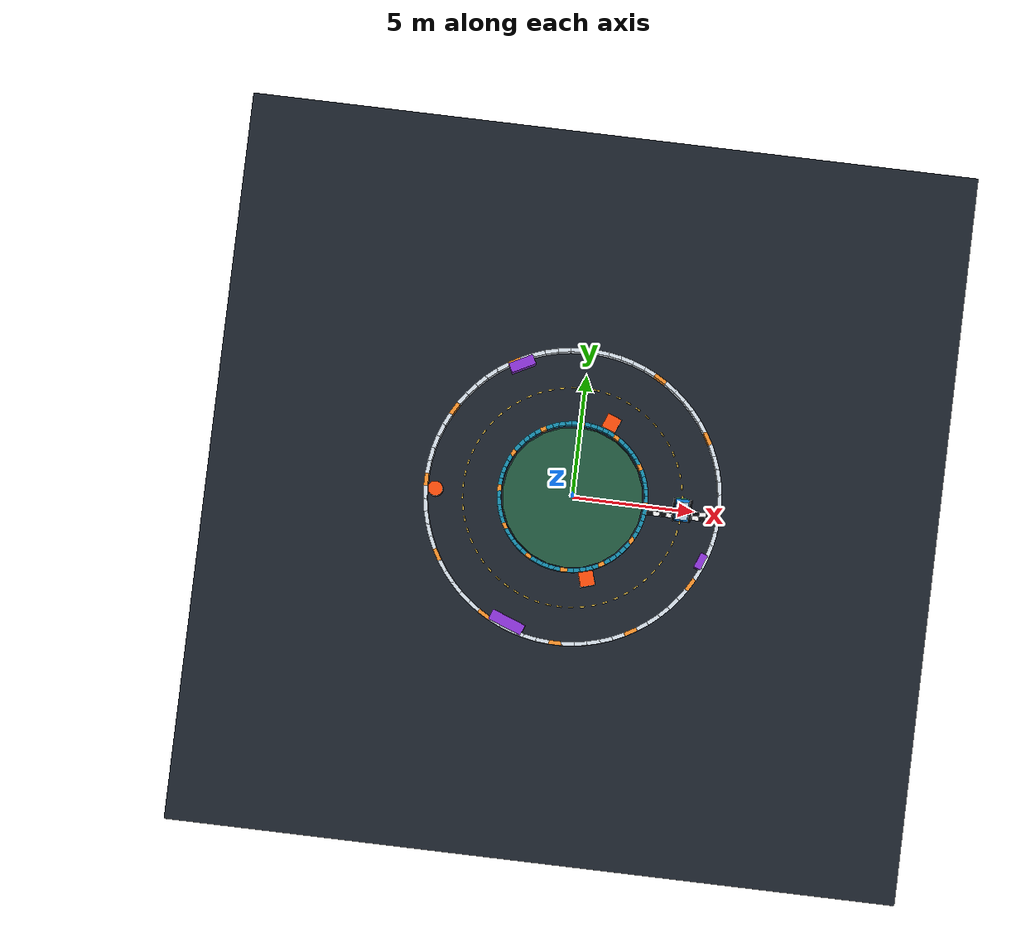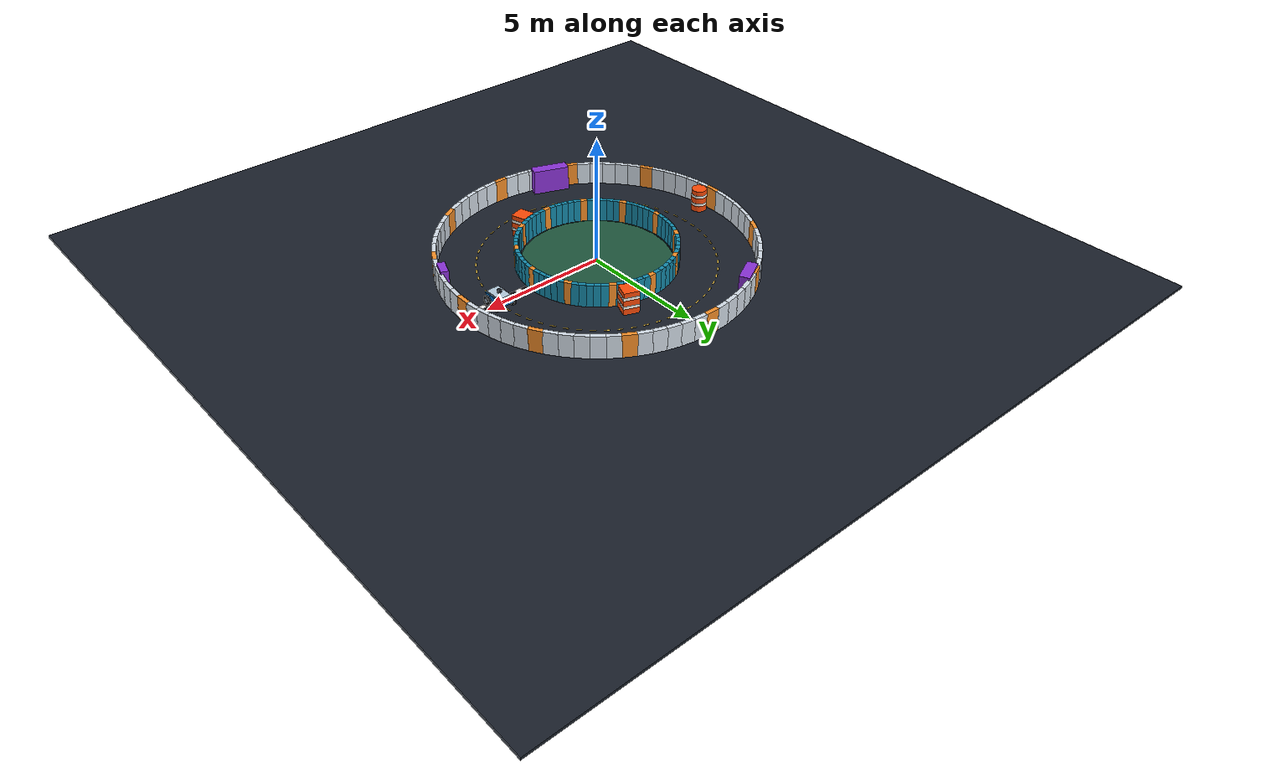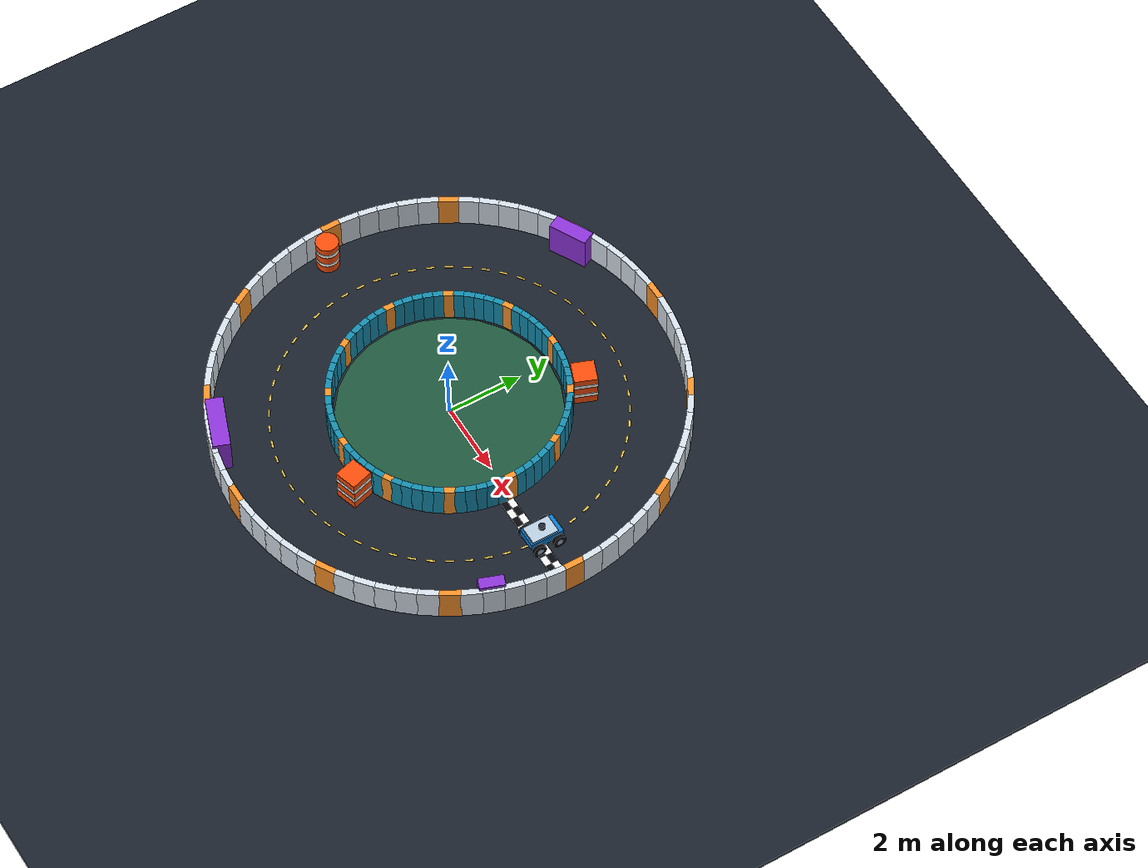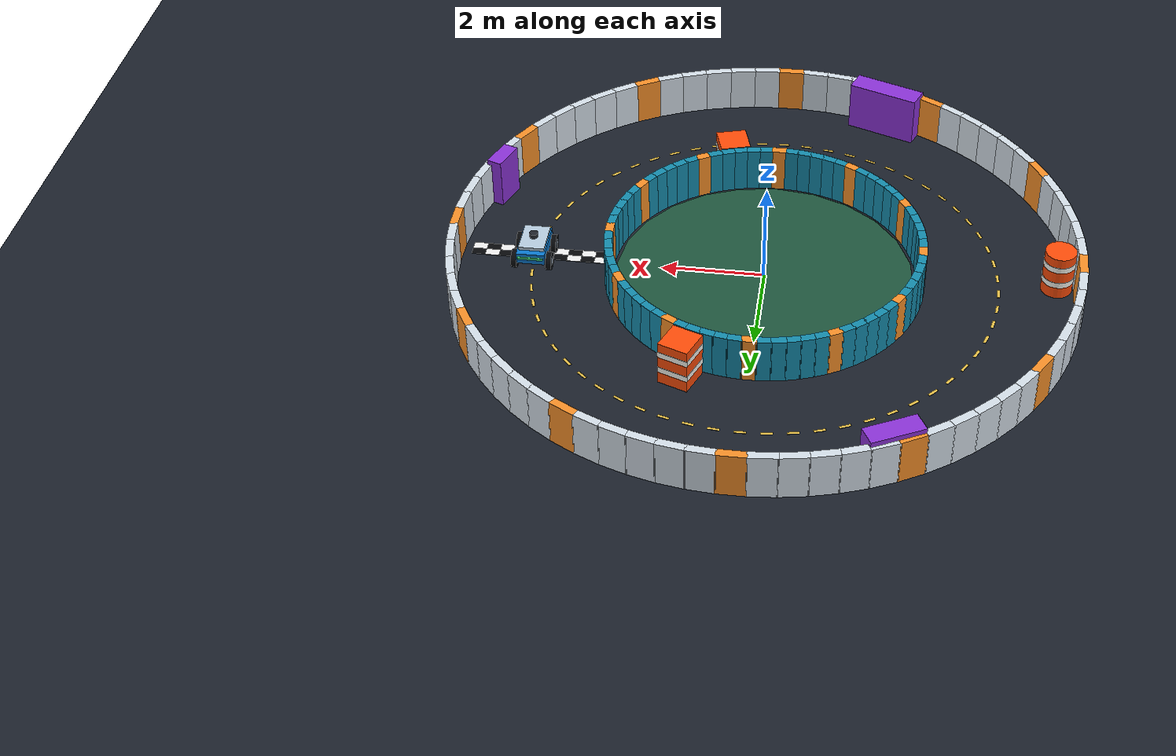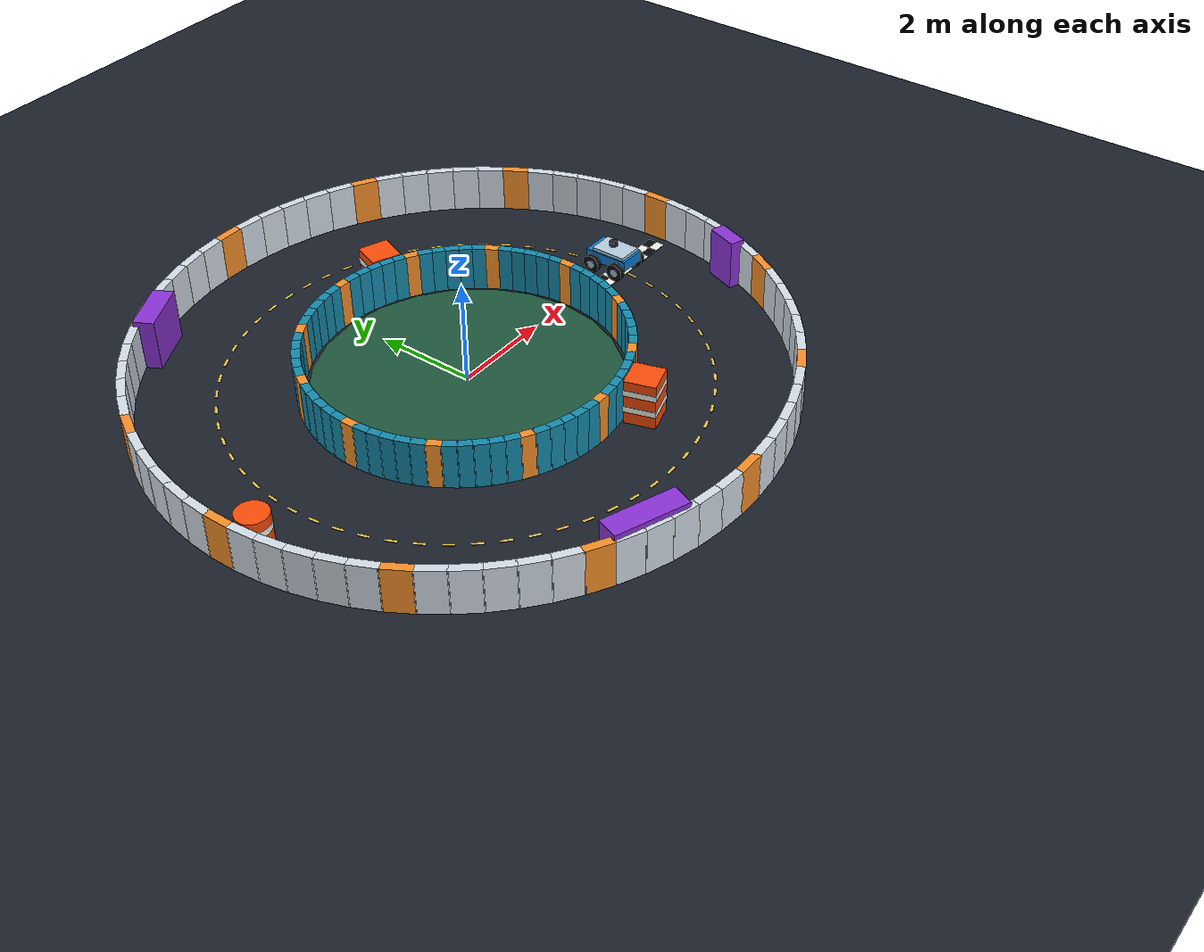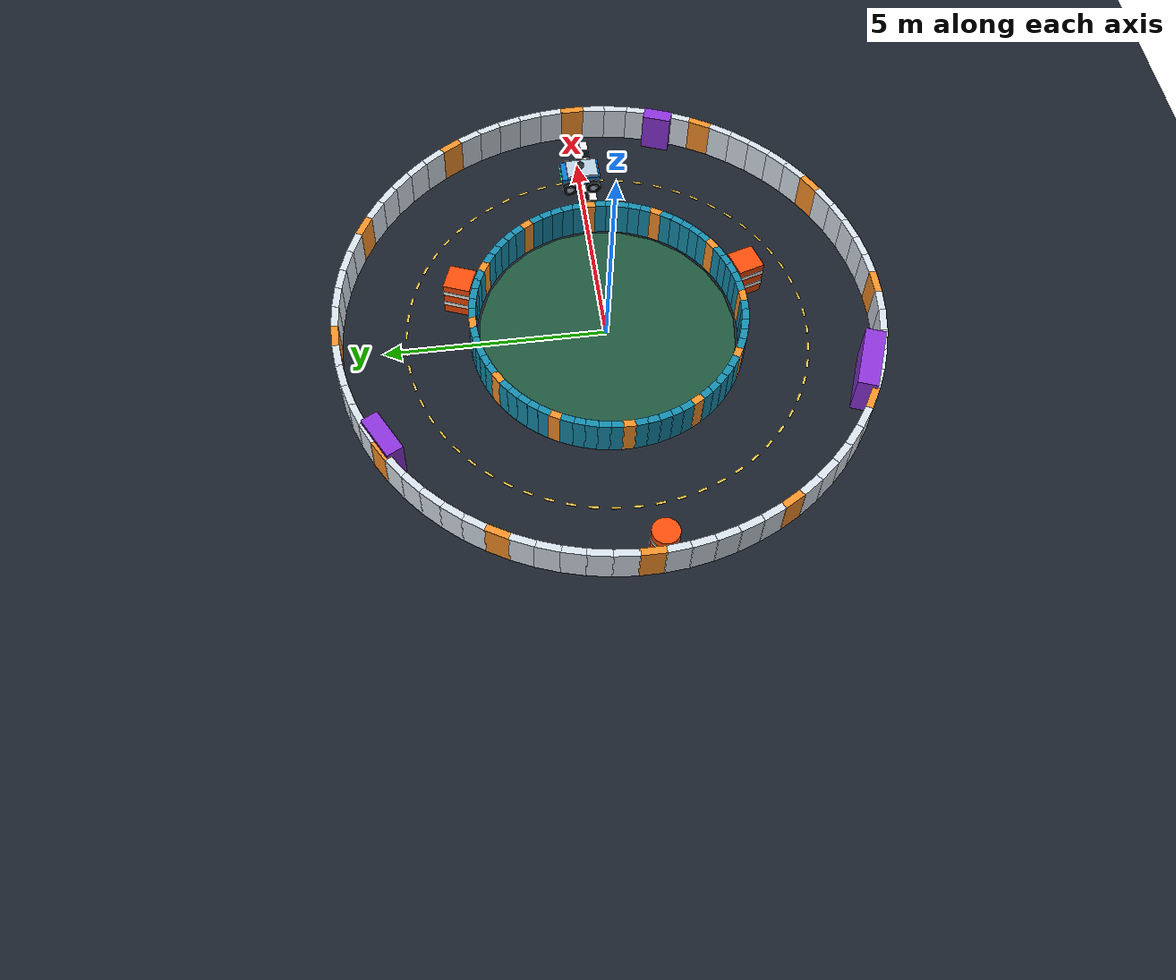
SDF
<?xml version='1.0' encoding='utf-8'?>
<sdf version="1.9">
  <world name="loop_course">
    <physics name="physics" type="ignored">
      <max_step_size>0.002</max_step_size>
      <real_time_factor>1.0</real_time_factor>
    </physics>
    <plugin filename="gz-sim-physics-system" name="gz::sim::systems::Physics" />
    <plugin filename="gz-sim-user-commands-system" name="gz::sim::systems::UserCommands" />
    <plugin filename="gz-sim-scene-broadcaster-system" name="gz::sim::systems::SceneBroadcaster" />
    <plugin filename="gz-sim-contact-system" name="gz::sim::systems::Contact" />
    <plugin filename="gz-sim-imu-system" name="gz::sim::systems::Imu" />
    <plugin filename="gz-sim-sensors-system" name="gz::sim::systems::Sensors">
      <render_engine>ogre2</render_engine>
    </plugin>
    <scene>
      <ambient>0.65 0.65 0.65 1</ambient>
      <background>0.12 0.16 0.22 1</background>
      <shadows>true</shadows>
    </scene>
    <light name="sun" type="directional">
      <pose>0 0 12 0 0 0</pose>
      <diffuse>0.9 0.9 0.85 1</diffuse>
      <specular>0.2 0.2 0.2 1</specular>
      <direction>-0.4 0.2 -0.9</direction>
      <cast_shadows>true</cast_shadows>
    </light>
    <gui fullscreen="false">
      <plugin filename="MinimalScene" name="3D View">
        <engine>ogre2</engine>
        <scene>scene</scene>
        <camera_pose>10 -13 14 0 0.73 2.22</camera_pose>
        <gz-gui>
          <property type="string" key="state">docked</property>
        </gz-gui>
      </plugin>
      <plugin filename="GzSceneManager" name="GzSceneManager" />
      <plugin filename="InteractiveViewControl" name="InteractiveViewControl" />
      <plugin filename="CameraTracking" name="CameraTracking" />
      <plugin filename="EntityContextMenuPlugin" name="EntityContextMenuPlugin" />
      <plugin filename="WorldControl" name="WorldControl">
        <play_pause>true</play_pause>
        <start_paused>false</start_paused>
      </plugin>
      <plugin filename="WorldStats" name="WorldStats">
        <sim_time>true</sim_time>
        <real_time>true</real_time>
        <real_time_factor>true</real_time_factor>
      </plugin>
    </gui>
    <model name="ground">
      <static>true</static>
      <link name="ground">
        <collision name="ground_collision">
          <pose>0 0 -0.05 0 0 0</pose>
          <geometry>
            <box>
              <size>30 30 0.1</size>
            </box>
          </geometry>
        </collision>
        <visual name="ground_visual">
          <pose>0 0 -0.05 0 0 0</pose>
          <geometry>
            <box>
              <size>30 30 0.1</size>
            </box>
          </geometry>
          <material>
            <ambient>0.105 0.13 0.17 1</ambient>
            <diffuse>0.105 0.13 0.17 1</diffuse>
          </material>
        </visual>
      </link>
    </model>
    <model name="island">
      <static>true</static>
      <link name="island">
        <visual name="grass">
          <pose>0 0 0.005 0 0 0</pose>
          <geometry>
            <cylinder>
              <radius>2.88</radius>
              <length>0.02</length>
            </cylinder>
          </geometry>
          <material>
            <ambient>0.12 0.34 0.24 1</ambient>
            <diffuse>0.12 0.34 0.24 1</diffuse>
          </material>
        </visual>
      </link>
    </model>
    <model name="inner_wall">
      <static>true</static>
      <link name="wall">
        <collision name="wall_0">
          <pose>3.0 0.0 0.45 0 0 1.5707963267948966</pose>
          <geometry>
            <box>
              <size>0.2869656574510724 0.16 0.9</size>
            </box>
          </geometry>
        </collision>
        <visual name="wall_visual_0">
          <pose>3.0 0.0 0.45 0 0 1.5707963267948966</pose>
          <geometry>
            <box>
              <size>0.2869656574510724 0.16 0.9</size>
            </box>
          </geometry>
          <material>
            <ambient>0.98 0.57 0.16 1</ambient>
            <diffuse>0.98 0.57 0.16 1</diffuse>
          </material>
        </visual>
        <collision name="wall_1">
          <pose>2.988584094275237 0.2614672282429745 0.45 0 0 1.658062789394613</pose>
          <geometry>
            <box>
              <size>0.2869656574510724 0.16 0.9</size>
            </box>
          </geometry>
        </collision>
        <visual name="wall_visual_1">
          <pose>2.988584094275237 0.2614672282429745 0.45 0 0 1.658062789394613</pose>
          <geometry>
            <box>
              <size>0.2869656574510724 0.16 0.9</size>
            </box>
          </geometry>
          <material>
            <ambient>0.08 0.55 0.68 1</ambient>
            <diffuse>0.08 0.55 0.68 1</diffuse>
          </material>
        </visual>
        <collision name="wall_2">
          <pose>2.954423259036624 0.520944533000791 0.45 0 0 1.7453292519943295</pose>
          <geometry>
            <box>
              <size>0.2869656574510724 0.16 0.9</size>
            </box>
          </geometry>
        </collision>
        <visual name="wall_visual_2">
          <pose>2.954423259036624 0.520944533000791 0.45 0 0 1.7453292519943295</pose>
          <geometry>
            <box>
              <size>0.2869656574510724 0.16 0.9</size>
            </box>
          </geometry>
          <material>
            <ambient>0.08 0.55 0.68 1</ambient>
            <diffuse>0.08 0.55 0.68 1</diffuse>
          </material>
        </visual>
        <collision name="wall_3">
          <pose>2.897777478867205 0.7764571353075622 0.45 0 0 1.832595714594046</pose>
          <geometry>
            <box>
              <size>0.2869656574510724 0.16 0.9</size>
            </box>
          </geometry>
        </collision>
        <visual name="wall_visual_3">
          <pose>2.897777478867205 0.7764571353075622 0.45 0 0 1.832595714594046</pose>
          <geometry>
            <box>
              <size>0.2869656574510724 0.16 0.9</size>
            </box>
          </geometry>
          <material>
            <ambient>0.08 0.55 0.68 1</ambient>
            <diffuse>0.08 0.55 0.68 1</diffuse>
          </material>
        </visual>
        <collision name="wall_4">
          <pose>2.8190778623577253 1.0260604299770062 0.45 0 0 1.9198621771937625</pose>
          <geometry>
            <box>
              <size>0.2869656574510724 0.16 0.9</size>
            </box>
          </geometry>
        </collision>
        <visual name="wall_visual_4">
          <pose>2.8190778623577253 1.0260604299770062 0.45 0 0 1.9198621771937625</pose>
          <geometry>
            <box>
              <size>0.2869656574510724 0.16 0.9</size>
            </box>
          </geometry>
          <material>
            <ambient>0.08 0.55 0.68 1</ambient>
            <diffuse>0.08 0.55 0.68 1</diffuse>
          </material>
        </visual>
        <collision name="wall_5">
          <pose>2.7189233611099497 1.2678547852220983 0.45 0 0 2.007128639793479</pose>
          <geometry>
            <box>
              <size>0.2869656574510724 0.16 0.9</size>
            </box>
          </geometry>
        </collision>
        <visual name="wall_visual_5">
          <pose>2.7189233611099497 1.2678547852220983 0.45 0 0 2.007128639793479</pose>
          <geometry>
            <box>
              <size>0.2869656574510724 0.16 0.9</size>
            </box>
          </geometry>
          <material>
            <ambient>0.08 0.55 0.68 1</ambient>
            <diffuse>0.08 0.55 0.68 1</diffuse>
          </material>
        </visual>
        <collision name="wall_6">
          <pose>2.598076211353316 1.4999999999999998 0.45 0 0 2.0943951023931953</pose>
          <geometry>
            <box>
              <size>0.2869656574510724 0.16 0.9</size>
            </box>
          </geometry>
        </collision>
        <visual name="wall_visual_6">
          <pose>2.598076211353316 1.4999999999999998 0.45 0 0 2.0943951023931953</pose>
          <geometry>
            <box>
              <size>0.2869656574510724 0.16 0.9</size>
            </box>
          </geometry>
          <material>
            <ambient>0.98 0.57 0.16 1</ambient>
            <diffuse>0.98 0.57 0.16 1</diffuse>
          </material>
        </visual>
        <collision name="wall_7">
          <pose>2.4574561328669753 1.7207293090531381 0.45 0 0 2.181661564992912</pose>
          <geometry>
            <box>
              <size>0.2869656574510724 0.16 0.9</size>
            </box>
          </geometry>
        </collision>
        <visual name="wall_visual_7">
          <pose>2.4574561328669753 1.7207293090531381 0.45 0 0 2.181661564992912</pose>
          <geometry>
            <box>
              <size>0.2869656574510724 0.16 0.9</size>
            </box>
          </geometry>
          <material>
            <ambient>0.08 0.55 0.68 1</ambient>
            <diffuse>0.08 0.55 0.68 1</diffuse>
          </material>
        </visual>
        <collision name="wall_8">
          <pose>2.298133329356934 1.9283628290596178 0.45 0 0 2.2689280275926285</pose>
          <geometry>
            <box>
              <size>0.2869656574510724 0.16 0.9</size>
            </box>
          </geometry>
        </collision>
        <visual name="wall_visual_8">
          <pose>2.298133329356934 1.9283628290596178 0.45 0 0 2.2689280275926285</pose>
          <geometry>
            <box>
              <size>0.2869656574510724 0.16 0.9</size>
            </box>
          </geometry>
          <material>
            <ambient>0.08 0.55 0.68 1</ambient>
            <diffuse>0.08 0.55 0.68 1</diffuse>
          </material>
        </visual>
        <collision name="wall_9">
          <pose>2.121320343559643 2.1213203435596424 0.45 0 0 2.356194490192345</pose>
          <geometry>
            <box>
              <size>0.2869656574510724 0.16 0.9</size>
            </box>
          </geometry>
        </collision>
        <visual name="wall_visual_9">
          <pose>2.121320343559643 2.1213203435596424 0.45 0 0 2.356194490192345</pose>
          <geometry>
            <box>
              <size>0.2869656574510724 0.16 0.9</size>
            </box>
          </geometry>
          <material>
            <ambient>0.08 0.55 0.68 1</ambient>
            <diffuse>0.08 0.55 0.68 1</diffuse>
          </material>
        </visual>
        <collision name="wall_10">
          <pose>1.9283628290596182 2.298133329356934 0.45 0 0 2.443460952792061</pose>
          <geometry>
            <box>
              <size>0.2869656574510724 0.16 0.9</size>
            </box>
          </geometry>
        </collision>
        <visual name="wall_visual_10">
          <pose>1.9283628290596182 2.298133329356934 0.45 0 0 2.443460952792061</pose>
          <geometry>
            <box>
              <size>0.2869656574510724 0.16 0.9</size>
            </box>
          </geometry>
          <material>
            <ambient>0.08 0.55 0.68 1</ambient>
            <diffuse>0.08 0.55 0.68 1</diffuse>
          </material>
        </visual>
        <collision name="wall_11">
          <pose>1.7207293090531386 2.457456132866975 0.45 0 0 2.5307274153917776</pose>
          <geometry>
            <box>
              <size>0.2869656574510724 0.16 0.9</size>
            </box>
          </geometry>
        </collision>
        <visual name="wall_visual_11">
          <pose>1.7207293090531386 2.457456132866975 0.45 0 0 2.5307274153917776</pose>
          <geometry>
            <box>
              <size>0.2869656574510724 0.16 0.9</size>
            </box>
          </geometry>
          <material>
            <ambient>0.08 0.55 0.68 1</ambient>
            <diffuse>0.08 0.55 0.68 1</diffuse>
          </material>
        </visual>
        <collision name="wall_12">
          <pose>1.5000000000000004 2.598076211353316 0.45 0 0 2.617993877991494</pose>
          <geometry>
            <box>
              <size>0.2869656574510724 0.16 0.9</size>
            </box>
          </geometry>
        </collision>
        <visual name="wall_visual_12">
          <pose>1.5000000000000004 2.598076211353316 0.45 0 0 2.617993877991494</pose>
          <geometry>
            <box>
              <size>0.2869656574510724 0.16 0.9</size>
            </box>
          </geometry>
          <material>
            <ambient>0.98 0.57 0.16 1</ambient>
            <diffuse>0.98 0.57 0.16 1</diffuse>
          </material>
        </visual>
        <collision name="wall_13">
          <pose>1.2678547852220983 2.7189233611099497 0.45 0 0 2.705260340591211</pose>
          <geometry>
            <box>
              <size>0.2869656574510724 0.16 0.9</size>
            </box>
          </geometry>
        </collision>
        <visual name="wall_visual_13">
          <pose>1.2678547852220983 2.7189233611099497 0.45 0 0 2.705260340591211</pose>
          <geometry>
            <box>
              <size>0.2869656574510724 0.16 0.9</size>
            </box>
          </geometry>
          <material>
            <ambient>0.08 0.55 0.68 1</ambient>
            <diffuse>0.08 0.55 0.68 1</diffuse>
          </material>
        </visual>
        <collision name="wall_14">
          <pose>1.0260604299770064 2.819077862357725 0.45 0 0 2.792526803190927</pose>
          <geometry>
            <box>
              <size>0.2869656574510724 0.16 0.9</size>
            </box>
          </geometry>
        </collision>
        <visual name="wall_visual_14">
          <pose>1.0260604299770064 2.819077862357725 0.45 0 0 2.792526803190927</pose>
          <geometry>
            <box>
              <size>0.2869656574510724 0.16 0.9</size>
            </box>
          </geometry>
          <material>
            <ambient>0.08 0.55 0.68 1</ambient>
            <diffuse>0.08 0.55 0.68 1</diffuse>
          </material>
        </visual>
        <collision name="wall_15">
          <pose>0.7764571353075629 2.8977774788672046 0.45 0 0 2.8797932657906435</pose>
          <geometry>
            <box>
              <size>0.2869656574510724 0.16 0.9</size>
            </box>
          </geometry>
        </collision>
        <visual name="wall_visual_15">
          <pose>0.7764571353075629 2.8977774788672046 0.45 0 0 2.8797932657906435</pose>
          <geometry>
            <box>
              <size>0.2869656574510724 0.16 0.9</size>
            </box>
          </geometry>
          <material>
            <ambient>0.08 0.55 0.68 1</ambient>
            <diffuse>0.08 0.55 0.68 1</diffuse>
          </material>
        </visual>
        <collision name="wall_16">
          <pose>0.5209445330007912 2.954423259036624 0.45 0 0 2.9670597283903604</pose>
          <geometry>
            <box>
              <size>0.2869656574510724 0.16 0.9</size>
            </box>
          </geometry>
        </collision>
        <visual name="wall_visual_16">
          <pose>0.5209445330007912 2.954423259036624 0.45 0 0 2.9670597283903604</pose>
          <geometry>
            <box>
              <size>0.2869656574510724 0.16 0.9</size>
            </box>
          </geometry>
          <material>
            <ambient>0.08 0.55 0.68 1</ambient>
            <diffuse>0.08 0.55 0.68 1</diffuse>
          </material>
        </visual>
        <collision name="wall_17">
          <pose>0.2614672282429744 2.988584094275237 0.45 0 0 3.0543261909900767</pose>
          <geometry>
            <box>
              <size>0.2869656574510724 0.16 0.9</size>
            </box>
          </geometry>
        </collision>
        <visual name="wall_visual_17">
          <pose>0.2614672282429744 2.988584094275237 0.45 0 0 3.0543261909900767</pose>
          <geometry>
            <box>
              <size>0.2869656574510724 0.16 0.9</size>
            </box>
          </geometry>
          <material>
            <ambient>0.08 0.55 0.68 1</ambient>
            <diffuse>0.08 0.55 0.68 1</diffuse>
          </material>
        </visual>
        <collision name="wall_18">
          <pose>1.8369701987210297e-16 3.0 0.45 0 0 3.141592653589793</pose>
          <geometry>
            <box>
              <size>0.2869656574510724 0.16 0.9</size>
            </box>
          </geometry>
        </collision>
        <visual name="wall_visual_18">
          <pose>1.8369701987210297e-16 3.0 0.45 0 0 3.141592653589793</pose>
          <geometry>
            <box>
              <size>0.2869656574510724 0.16 0.9</size>
            </box>
          </geometry>
          <material>
            <ambient>0.98 0.57 0.16 1</ambient>
            <diffuse>0.98 0.57 0.16 1</diffuse>
          </material>
        </visual>
        <collision name="wall_19">
          <pose>-0.261467228242974 2.988584094275237 0.45 0 0 3.2288591161895095</pose>
          <geometry>
            <box>
              <size>0.2869656574510724 0.16 0.9</size>
            </box>
          </geometry>
        </collision>
        <visual name="wall_visual_19">
          <pose>-0.261467228242974 2.988584094275237 0.45 0 0 3.2288591161895095</pose>
          <geometry>
            <box>
              <size>0.2869656574510724 0.16 0.9</size>
            </box>
          </geometry>
          <material>
            <ambient>0.08 0.55 0.68 1</ambient>
            <diffuse>0.08 0.55 0.68 1</diffuse>
          </material>
        </visual>
        <collision name="wall_20">
          <pose>-0.5209445330007909 2.954423259036624 0.45 0 0 3.316125578789226</pose>
          <geometry>
            <box>
              <size>0.2869656574510724 0.16 0.9</size>
            </box>
          </geometry>
        </collision>
        <visual name="wall_visual_20">
          <pose>-0.5209445330007909 2.954423259036624 0.45 0 0 3.316125578789226</pose>
          <geometry>
            <box>
              <size>0.2869656574510724 0.16 0.9</size>
            </box>
          </geometry>
          <material>
            <ambient>0.08 0.55 0.68 1</ambient>
            <diffuse>0.08 0.55 0.68 1</diffuse>
          </material>
        </visual>
        <collision name="wall_21">
          <pose>-0.7764571353075626 2.897777478867205 0.45 0 0 3.4033920413889427</pose>
          <geometry>
            <box>
              <size>0.2869656574510724 0.16 0.9</size>
            </box>
          </geometry>
        </collision>
        <visual name="wall_visual_21">
          <pose>-0.7764571353075626 2.897777478867205 0.45 0 0 3.4033920413889427</pose>
          <geometry>
            <box>
              <size>0.2869656574510724 0.16 0.9</size>
            </box>
          </geometry>
          <material>
            <ambient>0.08 0.55 0.68 1</ambient>
            <diffuse>0.08 0.55 0.68 1</diffuse>
          </material>
        </visual>
        <collision name="wall_22">
          <pose>-1.0260604299770055 2.8190778623577253 0.45 0 0 3.4906585039886586</pose>
          <geometry>
            <box>
              <size>0.2869656574510724 0.16 0.9</size>
            </box>
          </geometry>
        </collision>
        <visual name="wall_visual_22">
          <pose>-1.0260604299770055 2.8190778623577253 0.45 0 0 3.4906585039886586</pose>
          <geometry>
            <box>
              <size>0.2869656574510724 0.16 0.9</size>
            </box>
          </geometry>
          <material>
            <ambient>0.08 0.55 0.68 1</ambient>
            <diffuse>0.08 0.55 0.68 1</diffuse>
          </material>
        </visual>
        <collision name="wall_23">
          <pose>-1.267854785222098 2.71892336110995 0.45 0 0 3.5779249665883754</pose>
          <geometry>
            <box>
              <size>0.2869656574510724 0.16 0.9</size>
            </box>
          </geometry>
        </collision>
        <visual name="wall_visual_23">
          <pose>-1.267854785222098 2.71892336110995 0.45 0 0 3.5779249665883754</pose>
          <geometry>
            <box>
              <size>0.2869656574510724 0.16 0.9</size>
            </box>
          </geometry>
          <material>
            <ambient>0.08 0.55 0.68 1</ambient>
            <diffuse>0.08 0.55 0.68 1</diffuse>
          </material>
        </visual>
        <collision name="wall_24">
          <pose>-1.4999999999999993 2.598076211353316 0.45 0 0 3.665191429188092</pose>
          <geometry>
            <box>
              <size>0.2869656574510724 0.16 0.9</size>
            </box>
          </geometry>
        </collision>
        <visual name="wall_visual_24">
          <pose>-1.4999999999999993 2.598076211353316 0.45 0 0 3.665191429188092</pose>
          <geometry>
            <box>
              <size>0.2869656574510724 0.16 0.9</size>
            </box>
          </geometry>
          <material>
            <ambient>0.98 0.57 0.16 1</ambient>
            <diffuse>0.98 0.57 0.16 1</diffuse>
          </material>
        </visual>
        <collision name="wall_25">
          <pose>-1.7207293090531386 2.457456132866975 0.45 0 0 3.7524578917878086</pose>
          <geometry>
            <box>
              <size>0.2869656574510724 0.16 0.9</size>
            </box>
          </geometry>
        </collision>
        <visual name="wall_visual_25">
          <pose>-1.7207293090531386 2.457456132866975 0.45 0 0 3.7524578917878086</pose>
          <geometry>
            <box>
              <size>0.2869656574510724 0.16 0.9</size>
            </box>
          </geometry>
          <material>
            <ambient>0.08 0.55 0.68 1</ambient>
            <diffuse>0.08 0.55 0.68 1</diffuse>
          </material>
        </visual>
        <collision name="wall_26">
          <pose>-1.9283628290596182 2.298133329356934 0.45 0 0 3.839724354387525</pose>
          <geometry>
            <box>
              <size>0.2869656574510724 0.16 0.9</size>
            </box>
          </geometry>
        </collision>
        <visual name="wall_visual_26">
          <pose>-1.9283628290596182 2.298133329356934 0.45 0 0 3.839724354387525</pose>
          <geometry>
            <box>
              <size>0.2869656574510724 0.16 0.9</size>
            </box>
          </geometry>
          <material>
            <ambient>0.08 0.55 0.68 1</ambient>
            <diffuse>0.08 0.55 0.68 1</diffuse>
          </material>
        </visual>
        <collision name="wall_27">
          <pose>-2.1213203435596424 2.121320343559643 0.45 0 0 3.9269908169872414</pose>
          <geometry>
            <box>
              <size>0.2869656574510724 0.16 0.9</size>
            </box>
          </geometry>
        </collision>
        <visual name="wall_visual_27">
          <pose>-2.1213203435596424 2.121320343559643 0.45 0 0 3.9269908169872414</pose>
          <geometry>
            <box>
              <size>0.2869656574510724 0.16 0.9</size>
            </box>
          </geometry>
          <material>
            <ambient>0.08 0.55 0.68 1</ambient>
            <diffuse>0.08 0.55 0.68 1</diffuse>
          </material>
        </visual>
        <collision name="wall_28">
          <pose>-2.2981333293569337 1.9283628290596184 0.45 0 0 4.014257279586958</pose>
          <geometry>
            <box>
              <size>0.2869656574510724 0.16 0.9</size>
            </box>
          </geometry>
        </collision>
        <visual name="wall_visual_28">
          <pose>-2.2981333293569337 1.9283628290596184 0.45 0 0 4.014257279586958</pose>
          <geometry>
            <box>
              <size>0.2869656574510724 0.16 0.9</size>
            </box>
          </geometry>
          <material>
            <ambient>0.08 0.55 0.68 1</ambient>
            <diffuse>0.08 0.55 0.68 1</diffuse>
          </material>
        </visual>
        <collision name="wall_29">
          <pose>-2.4574561328669757 1.7207293090531377 0.45 0 0 4.101523742186675</pose>
          <geometry>
            <box>
              <size>0.2869656574510724 0.16 0.9</size>
            </box>
          </geometry>
        </collision>
        <visual name="wall_visual_29">
          <pose>-2.4574561328669757 1.7207293090531377 0.45 0 0 4.101523742186675</pose>
          <geometry>
            <box>
              <size>0.2869656574510724 0.16 0.9</size>
            </box>
          </geometry>
          <material>
            <ambient>0.08 0.55 0.68 1</ambient>
            <diffuse>0.08 0.55 0.68 1</diffuse>
          </material>
        </visual>
        <collision name="wall_30">
          <pose>-2.5980762113533156 1.5000000000000009 0.45 0 0 4.1887902047863905</pose>
          <geometry>
            <box>
              <size>0.2869656574510724 0.16 0.9</size>
            </box>
          </geometry>
        </collision>
        <visual name="wall_visual_30">
          <pose>-2.5980762113533156 1.5000000000000009 0.45 0 0 4.1887902047863905</pose>
          <geometry>
            <box>
              <size>0.2869656574510724 0.16 0.9</size>
            </box>
          </geometry>
          <material>
            <ambient>0.98 0.57 0.16 1</ambient>
            <diffuse>0.98 0.57 0.16 1</diffuse>
          </material>
        </visual>
        <collision name="wall_31">
          <pose>-2.7189233611099497 1.2678547852220985 0.45 0 0 4.276056667386108</pose>
          <geometry>
            <box>
              <size>0.2869656574510724 0.16 0.9</size>
            </box>
          </geometry>
        </collision>
        <visual name="wall_visual_31">
          <pose>-2.7189233611099497 1.2678547852220985 0.45 0 0 4.276056667386108</pose>
          <geometry>
            <box>
              <size>0.2869656574510724 0.16 0.9</size>
            </box>
          </geometry>
          <material>
            <ambient>0.08 0.55 0.68 1</ambient>
            <diffuse>0.08 0.55 0.68 1</diffuse>
          </material>
        </visual>
        <collision name="wall_32">
          <pose>-2.819077862357725 1.0260604299770066 0.45 0 0 4.363323129985824</pose>
          <geometry>
            <box>
              <size>0.2869656574510724 0.16 0.9</size>
            </box>
          </geometry>
        </collision>
        <visual name="wall_visual_32">
          <pose>-2.819077862357725 1.0260604299770066 0.45 0 0 4.363323129985824</pose>
          <geometry>
            <box>
              <size>0.2869656574510724 0.16 0.9</size>
            </box>
          </geometry>
          <material>
            <ambient>0.08 0.55 0.68 1</ambient>
            <diffuse>0.08 0.55 0.68 1</diffuse>
          </material>
        </visual>
        <collision name="wall_33">
          <pose>-2.897777478867205 0.7764571353075618 0.45 0 0 4.4505895925855405</pose>
          <geometry>
            <box>
              <size>0.2869656574510724 0.16 0.9</size>
            </box>
          </geometry>
        </collision>
        <visual name="wall_visual_33">
          <pose>-2.897777478867205 0.7764571353075618 0.45 0 0 4.4505895925855405</pose>
          <geometry>
            <box>
              <size>0.2869656574510724 0.16 0.9</size>
            </box>
          </geometry>
          <material>
            <ambient>0.08 0.55 0.68 1</ambient>
            <diffuse>0.08 0.55 0.68 1</diffuse>
          </material>
        </visual>
        <collision name="wall_34">
          <pose>-2.954423259036624 0.5209445330007908 0.45 0 0 4.537856055185257</pose>
          <geometry>
            <box>
              <size>0.2869656574510724 0.16 0.9</size>
            </box>
          </geometry>
        </collision>
        <visual name="wall_visual_34">
          <pose>-2.954423259036624 0.5209445330007908 0.45 0 0 4.537856055185257</pose>
          <geometry>
            <box>
              <size>0.2869656574510724 0.16 0.9</size>
            </box>
          </geometry>
          <material>
            <ambient>0.08 0.55 0.68 1</ambient>
            <diffuse>0.08 0.55 0.68 1</diffuse>
          </material>
        </visual>
        <collision name="wall_35">
          <pose>-2.988584094275237 0.2614672282429746 0.45 0 0 4.625122517784973</pose>
          <geometry>
            <box>
              <size>0.2869656574510724 0.16 0.9</size>
            </box>
          </geometry>
        </collision>
        <visual name="wall_visual_35">
          <pose>-2.988584094275237 0.2614672282429746 0.45 0 0 4.625122517784973</pose>
          <geometry>
            <box>
              <size>0.2869656574510724 0.16 0.9</size>
            </box>
          </geometry>
          <material>
            <ambient>0.08 0.55 0.68 1</ambient>
            <diffuse>0.08 0.55 0.68 1</diffuse>
          </material>
        </visual>
        <collision name="wall_36">
          <pose>-3.0 3.6739403974420594e-16 0.45 0 0 4.71238898038469</pose>
          <geometry>
            <box>
              <size>0.2869656574510724 0.16 0.9</size>
            </box>
          </geometry>
        </collision>
        <visual name="wall_visual_36">
          <pose>-3.0 3.6739403974420594e-16 0.45 0 0 4.71238898038469</pose>
          <geometry>
            <box>
              <size>0.2869656574510724 0.16 0.9</size>
            </box>
          </geometry>
          <material>
            <ambient>0.98 0.57 0.16 1</ambient>
            <diffuse>0.98 0.57 0.16 1</diffuse>
          </material>
        </visual>
        <collision name="wall_37">
          <pose>-2.988584094275237 -0.26146722824297386 0.45 0 0 4.799655442984406</pose>
          <geometry>
            <box>
              <size>0.2869656574510724 0.16 0.9</size>
            </box>
          </geometry>
        </collision>
        <visual name="wall_visual_37">
          <pose>-2.988584094275237 -0.26146722824297386 0.45 0 0 4.799655442984406</pose>
          <geometry>
            <box>
              <size>0.2869656574510724 0.16 0.9</size>
            </box>
          </geometry>
          <material>
            <ambient>0.08 0.55 0.68 1</ambient>
            <diffuse>0.08 0.55 0.68 1</diffuse>
          </material>
        </visual>
        <collision name="wall_38">
          <pose>-2.9544232590366244 -0.52094453300079 0.45 0 0 4.886921905584122</pose>
          <geometry>
            <box>
              <size>0.2869656574510724 0.16 0.9</size>
            </box>
          </geometry>
        </collision>
        <visual name="wall_visual_38">
          <pose>-2.9544232590366244 -0.52094453300079 0.45 0 0 4.886921905584122</pose>
          <geometry>
            <box>
              <size>0.2869656574510724 0.16 0.9</size>
            </box>
          </geometry>
          <material>
            <ambient>0.08 0.55 0.68 1</ambient>
            <diffuse>0.08 0.55 0.68 1</diffuse>
          </material>
        </visual>
        <collision name="wall_39">
          <pose>-2.897777478867205 -0.7764571353075611 0.45 0 0 4.974188368183839</pose>
          <geometry>
            <box>
              <size>0.2869656574510724 0.16 0.9</size>
            </box>
          </geometry>
        </collision>
        <visual name="wall_visual_39">
          <pose>-2.897777478867205 -0.7764571353075611 0.45 0 0 4.974188368183839</pose>
          <geometry>
            <box>
              <size>0.2869656574510724 0.16 0.9</size>
            </box>
          </geometry>
          <material>
            <ambient>0.08 0.55 0.68 1</ambient>
            <diffuse>0.08 0.55 0.68 1</diffuse>
          </material>
        </visual>
        <collision name="wall_40">
          <pose>-2.8190778623577253 -1.026060429977006 0.45 0 0 5.061454830783555</pose>
          <geometry>
            <box>
              <size>0.2869656574510724 0.16 0.9</size>
            </box>
          </geometry>
        </collision>
        <visual name="wall_visual_40">
          <pose>-2.8190778623577253 -1.026060429977006 0.45 0 0 5.061454830783555</pose>
          <geometry>
            <box>
              <size>0.2869656574510724 0.16 0.9</size>
            </box>
          </geometry>
          <material>
            <ambient>0.08 0.55 0.68 1</ambient>
            <diffuse>0.08 0.55 0.68 1</diffuse>
          </material>
        </visual>
        <collision name="wall_41">
          <pose>-2.718923361109951 -1.2678547852220967 0.45 0 0 5.148721293383272</pose>
          <geometry>
            <box>
              <size>0.2869656574510724 0.16 0.9</size>
            </box>
          </geometry>
        </collision>
        <visual name="wall_visual_41">
          <pose>-2.718923361109951 -1.2678547852220967 0.45 0 0 5.148721293383272</pose>
          <geometry>
            <box>
              <size>0.2869656574510724 0.16 0.9</size>
            </box>
          </geometry>
          <material>
            <ambient>0.08 0.55 0.68 1</ambient>
            <diffuse>0.08 0.55 0.68 1</diffuse>
          </material>
        </visual>
        <collision name="wall_42">
          <pose>-2.598076211353316 -1.5000000000000004 0.45 0 0 5.235987755982989</pose>
          <geometry>
            <box>
              <size>0.2869656574510724 0.16 0.9</size>
            </box>
          </geometry>
        </collision>
        <visual name="wall_visual_42">
          <pose>-2.598076211353316 -1.5000000000000004 0.45 0 0 5.235987755982989</pose>
          <geometry>
            <box>
              <size>0.2869656574510724 0.16 0.9</size>
            </box>
          </geometry>
          <material>
            <ambient>0.98 0.57 0.16 1</ambient>
            <diffuse>0.98 0.57 0.16 1</diffuse>
          </material>
        </visual>
        <collision name="wall_43">
          <pose>-2.457456132866976 -1.7207293090531375 0.45 0 0 5.323254218582704</pose>
          <geometry>
            <box>
              <size>0.2869656574510724 0.16 0.9</size>
            </box>
          </geometry>
        </collision>
        <visual name="wall_visual_43">
          <pose>-2.457456132866976 -1.7207293090531375 0.45 0 0 5.323254218582704</pose>
          <geometry>
            <box>
              <size>0.2869656574510724 0.16 0.9</size>
            </box>
          </geometry>
          <material>
            <ambient>0.08 0.55 0.68 1</ambient>
            <diffuse>0.08 0.55 0.68 1</diffuse>
          </material>
        </visual>
        <collision name="wall_44">
          <pose>-2.298133329356935 -1.9283628290596169 0.45 0 0 5.410520681182421</pose>
          <geometry>
            <box>
              <size>0.2869656574510724 0.16 0.9</size>
            </box>
          </geometry>
        </collision>
        <visual name="wall_visual_44">
          <pose>-2.298133329356935 -1.9283628290596169 0.45 0 0 5.410520681182421</pose>
          <geometry>
            <box>
              <size>0.2869656574510724 0.16 0.9</size>
            </box>
          </geometry>
          <material>
            <ambient>0.08 0.55 0.68 1</ambient>
            <diffuse>0.08 0.55 0.68 1</diffuse>
          </material>
        </visual>
        <collision name="wall_45">
          <pose>-2.121320343559643 -2.1213203435596424 0.45 0 0 5.497787143782138</pose>
          <geometry>
            <box>
              <size>0.2869656574510724 0.16 0.9</size>
            </box>
          </geometry>
        </collision>
        <visual name="wall_visual_45">
          <pose>-2.121320343559643 -2.1213203435596424 0.45 0 0 5.497787143782138</pose>
          <geometry>
            <box>
              <size>0.2869656574510724 0.16 0.9</size>
            </box>
          </geometry>
          <material>
            <ambient>0.08 0.55 0.68 1</ambient>
            <diffuse>0.08 0.55 0.68 1</diffuse>
          </material>
        </visual>
        <collision name="wall_46">
          <pose>-1.9283628290596184 -2.2981333293569337 0.45 0 0 5.585053606381854</pose>
          <geometry>
            <box>
              <size>0.2869656574510724 0.16 0.9</size>
            </box>
          </geometry>
        </collision>
        <visual name="wall_visual_46">
          <pose>-1.9283628290596184 -2.2981333293569337 0.45 0 0 5.585053606381854</pose>
          <geometry>
            <box>
              <size>0.2869656574510724 0.16 0.9</size>
            </box>
          </geometry>
          <material>
            <ambient>0.08 0.55 0.68 1</ambient>
            <diffuse>0.08 0.55 0.68 1</diffuse>
          </material>
        </visual>
        <collision name="wall_47">
          <pose>-1.7207293090531373 -2.4574561328669766 0.45 0 0 5.672320068981572</pose>
          <geometry>
            <box>
              <size>0.2869656574510724 0.16 0.9</size>
            </box>
          </geometry>
        </collision>
        <visual name="wall_visual_47">
          <pose>-1.7207293090531373 -2.4574561328669766 0.45 0 0 5.672320068981572</pose>
          <geometry>
            <box>
              <size>0.2869656574510724 0.16 0.9</size>
            </box>
          </geometry>
          <material>
            <ambient>0.08 0.55 0.68 1</ambient>
            <diffuse>0.08 0.55 0.68 1</diffuse>
          </material>
        </visual>
        <collision name="wall_48">
          <pose>-1.5000000000000013 -2.598076211353315 0.45 0 0 5.759586531581287</pose>
          <geometry>
            <box>
              <size>0.2869656574510724 0.16 0.9</size>
            </box>
          </geometry>
        </collision>
        <visual name="wall_visual_48">
          <pose>-1.5000000000000013 -2.598076211353315 0.45 0 0 5.759586531581287</pose>
          <geometry>
            <box>
              <size>0.2869656574510724 0.16 0.9</size>
            </box>
          </geometry>
          <material>
            <ambient>0.98 0.57 0.16 1</ambient>
            <diffuse>0.98 0.57 0.16 1</diffuse>
          </material>
        </visual>
        <collision name="wall_49">
          <pose>-1.2678547852220998 -2.7189233611099493 0.45 0 0 5.8468529941810035</pose>
          <geometry>
            <box>
              <size>0.2869656574510724 0.16 0.9</size>
            </box>
          </geometry>
        </collision>
        <visual name="wall_visual_49">
          <pose>-1.2678547852220998 -2.7189233611099493 0.45 0 0 5.8468529941810035</pose>
          <geometry>
            <box>
              <size>0.2869656574510724 0.16 0.9</size>
            </box>
          </geometry>
          <material>
            <ambient>0.08 0.55 0.68 1</ambient>
            <diffuse>0.08 0.55 0.68 1</diffuse>
          </material>
        </visual>
        <collision name="wall_50">
          <pose>-1.0260604299770058 -2.8190778623577253 0.45 0 0 5.934119456780721</pose>
          <geometry>
            <box>
              <size>0.2869656574510724 0.16 0.9</size>
            </box>
          </geometry>
        </collision>
        <visual name="wall_visual_50">
          <pose>-1.0260604299770058 -2.8190778623577253 0.45 0 0 5.934119456780721</pose>
          <geometry>
            <box>
              <size>0.2869656574510724 0.16 0.9</size>
            </box>
          </geometry>
          <material>
            <ambient>0.08 0.55 0.68 1</ambient>
            <diffuse>0.08 0.55 0.68 1</diffuse>
          </material>
        </visual>
        <collision name="wall_51">
          <pose>-0.7764571353075619 -2.897777478867205 0.45 0 0 6.021385919380437</pose>
          <geometry>
            <box>
              <size>0.2869656574510724 0.16 0.9</size>
            </box>
          </geometry>
        </collision>
        <visual name="wall_visual_51">
          <pose>-0.7764571353075619 -2.897777478867205 0.45 0 0 6.021385919380437</pose>
          <geometry>
            <box>
              <size>0.2869656574510724 0.16 0.9</size>
            </box>
          </geometry>
          <material>
            <ambient>0.08 0.55 0.68 1</ambient>
            <diffuse>0.08 0.55 0.68 1</diffuse>
          </material>
        </visual>
        <collision name="wall_52">
          <pose>-0.520944533000791 -2.954423259036624 0.45 0 0 6.1086523819801535</pose>
          <geometry>
            <box>
              <size>0.2869656574510724 0.16 0.9</size>
            </box>
          </geometry>
        </collision>
        <visual name="wall_visual_52">
          <pose>-0.520944533000791 -2.954423259036624 0.45 0 0 6.1086523819801535</pose>
          <geometry>
            <box>
              <size>0.2869656574510724 0.16 0.9</size>
            </box>
          </geometry>
          <material>
            <ambient>0.08 0.55 0.68 1</ambient>
            <diffuse>0.08 0.55 0.68 1</diffuse>
          </material>
        </visual>
        <collision name="wall_53">
          <pose>-0.26146722824297475 -2.988584094275237 0.45 0 0 6.19591884457987</pose>
          <geometry>
            <box>
              <size>0.2869656574510724 0.16 0.9</size>
            </box>
          </geometry>
        </collision>
        <visual name="wall_visual_53">
          <pose>-0.26146722824297475 -2.988584094275237 0.45 0 0 6.19591884457987</pose>
          <geometry>
            <box>
              <size>0.2869656574510724 0.16 0.9</size>
            </box>
          </geometry>
          <material>
            <ambient>0.08 0.55 0.68 1</ambient>
            <diffuse>0.08 0.55 0.68 1</diffuse>
          </material>
        </visual>
        <collision name="wall_54">
          <pose>-5.51091059616309e-16 -3.0 0.45 0 0 6.283185307179586</pose>
          <geometry>
            <box>
              <size>0.2869656574510724 0.16 0.9</size>
            </box>
          </geometry>
        </collision>
        <visual name="wall_visual_54">
          <pose>-5.51091059616309e-16 -3.0 0.45 0 0 6.283185307179586</pose>
          <geometry>
            <box>
              <size>0.2869656574510724 0.16 0.9</size>
            </box>
          </geometry>
          <material>
            <ambient>0.98 0.57 0.16 1</ambient>
            <diffuse>0.98 0.57 0.16 1</diffuse>
          </material>
        </visual>
        <collision name="wall_55">
          <pose>0.26146722824297364 -2.988584094275237 0.45 0 0 6.370451769779303</pose>
          <geometry>
            <box>
              <size>0.2869656574510724 0.16 0.9</size>
            </box>
          </geometry>
        </collision>
        <visual name="wall_visual_55">
          <pose>0.26146722824297364 -2.988584094275237 0.45 0 0 6.370451769779303</pose>
          <geometry>
            <box>
              <size>0.2869656574510724 0.16 0.9</size>
            </box>
          </geometry>
          <material>
            <ambient>0.08 0.55 0.68 1</ambient>
            <diffuse>0.08 0.55 0.68 1</diffuse>
          </material>
        </visual>
        <collision name="wall_56">
          <pose>0.5209445330007899 -2.9544232590366244 0.45 0 0 6.457718232379019</pose>
          <geometry>
            <box>
              <size>0.2869656574510724 0.16 0.9</size>
            </box>
          </geometry>
        </collision>
        <visual name="wall_visual_56">
          <pose>0.5209445330007899 -2.9544232590366244 0.45 0 0 6.457718232379019</pose>
          <geometry>
            <box>
              <size>0.2869656574510724 0.16 0.9</size>
            </box>
          </geometry>
          <material>
            <ambient>0.08 0.55 0.68 1</ambient>
            <diffuse>0.08 0.55 0.68 1</diffuse>
          </material>
        </visual>
        <collision name="wall_57">
          <pose>0.7764571353075609 -2.897777478867205 0.45 0 0 6.544984694978735</pose>
          <geometry>
            <box>
              <size>0.2869656574510724 0.16 0.9</size>
            </box>
          </geometry>
        </collision>
        <visual name="wall_visual_57">
          <pose>0.7764571353075609 -2.897777478867205 0.45 0 0 6.544984694978735</pose>
          <geometry>
            <box>
              <size>0.2869656574510724 0.16 0.9</size>
            </box>
          </geometry>
          <material>
            <ambient>0.08 0.55 0.68 1</ambient>
            <diffuse>0.08 0.55 0.68 1</diffuse>
          </material>
        </visual>
        <collision name="wall_58">
          <pose>1.026060429977007 -2.819077862357725 0.45 0 0 6.632251157578453</pose>
          <geometry>
            <box>
              <size>0.2869656574510724 0.16 0.9</size>
            </box>
          </geometry>
        </collision>
        <visual name="wall_visual_58">
          <pose>1.026060429977007 -2.819077862357725 0.45 0 0 6.632251157578453</pose>
          <geometry>
            <box>
              <size>0.2869656574510724 0.16 0.9</size>
            </box>
          </geometry>
          <material>
            <ambient>0.08 0.55 0.68 1</ambient>
            <diffuse>0.08 0.55 0.68 1</diffuse>
          </material>
        </visual>
        <collision name="wall_59">
          <pose>1.2678547852220965 -2.718923361109951 0.45 0 0 6.719517620178168</pose>
          <geometry>
            <box>
              <size>0.2869656574510724 0.16 0.9</size>
            </box>
          </geometry>
        </collision>
        <visual name="wall_visual_59">
          <pose>1.2678547852220965 -2.718923361109951 0.45 0 0 6.719517620178168</pose>
          <geometry>
            <box>
              <size>0.2869656574510724 0.16 0.9</size>
            </box>
          </geometry>
          <material>
            <ambient>0.08 0.55 0.68 1</ambient>
            <diffuse>0.08 0.55 0.68 1</diffuse>
          </material>
        </visual>
        <collision name="wall_60">
          <pose>1.499999999999998 -2.598076211353317 0.45 0 0 6.8067840827778845</pose>
          <geometry>
            <box>
              <size>0.2869656574510724 0.16 0.9</size>
            </box>
          </geometry>
        </collision>
        <visual name="wall_visual_60">
          <pose>1.499999999999998 -2.598076211353317 0.45 0 0 6.8067840827778845</pose>
          <geometry>
            <box>
              <size>0.2869656574510724 0.16 0.9</size>
            </box>
          </geometry>
          <material>
            <ambient>0.98 0.57 0.16 1</ambient>
            <diffuse>0.98 0.57 0.16 1</diffuse>
          </material>
        </visual>
        <collision name="wall_61">
          <pose>1.7207293090531381 -2.4574561328669753 0.45 0 0 6.894050545377602</pose>
          <geometry>
            <box>
              <size>0.2869656574510724 0.16 0.9</size>
            </box>
          </geometry>
        </collision>
        <visual name="wall_visual_61">
          <pose>1.7207293090531381 -2.4574561328669753 0.45 0 0 6.894050545377602</pose>
          <geometry>
            <box>
              <size>0.2869656574510724 0.16 0.9</size>
            </box>
          </geometry>
          <material>
            <ambient>0.08 0.55 0.68 1</ambient>
            <diffuse>0.08 0.55 0.68 1</diffuse>
          </material>
        </visual>
        <collision name="wall_62">
          <pose>1.9283628290596178 -2.2981333293569346 0.45 0 0 6.981317007977318</pose>
          <geometry>
            <box>
              <size>0.2869656574510724 0.16 0.9</size>
            </box>
          </geometry>
        </collision>
        <visual name="wall_visual_62">
          <pose>1.9283628290596178 -2.2981333293569346 0.45 0 0 6.981317007977318</pose>
          <geometry>
            <box>
              <size>0.2869656574510724 0.16 0.9</size>
            </box>
          </geometry>
          <material>
            <ambient>0.08 0.55 0.68 1</ambient>
            <diffuse>0.08 0.55 0.68 1</diffuse>
          </material>
        </visual>
        <collision name="wall_63">
          <pose>2.121320343559642 -2.121320343559643 0.45 0 0 7.0685834705770345</pose>
          <geometry>
            <box>
              <size>0.2869656574510724 0.16 0.9</size>
            </box>
          </geometry>
        </collision>
        <visual name="wall_visual_63">
          <pose>2.121320343559642 -2.121320343559643 0.45 0 0 7.0685834705770345</pose>
          <geometry>
            <box>
              <size>0.2869656574510724 0.16 0.9</size>
            </box>
          </geometry>
          <material>
            <ambient>0.08 0.55 0.68 1</ambient>
            <diffuse>0.08 0.55 0.68 1</diffuse>
          </material>
        </visual>
        <collision name="wall_64">
          <pose>2.2981333293569333 -1.9283628290596186 0.45 0 0 7.155849933176751</pose>
          <geometry>
            <box>
              <size>0.2869656574510724 0.16 0.9</size>
            </box>
          </geometry>
        </collision>
        <visual name="wall_visual_64">
          <pose>2.2981333293569333 -1.9283628290596186 0.45 0 0 7.155849933176751</pose>
          <geometry>
            <box>
              <size>0.2869656574510724 0.16 0.9</size>
            </box>
          </geometry>
          <material>
            <ambient>0.08 0.55 0.68 1</ambient>
            <diffuse>0.08 0.55 0.68 1</diffuse>
          </material>
        </visual>
        <collision name="wall_65">
          <pose>2.457456132866975 -1.7207293090531395 0.45 0 0 7.243116395776467</pose>
          <geometry>
            <box>
              <size>0.2869656574510724 0.16 0.9</size>
            </box>
          </geometry>
        </collision>
        <visual name="wall_visual_65">
          <pose>2.457456132866975 -1.7207293090531395 0.45 0 0 7.243116395776467</pose>
          <geometry>
            <box>
              <size>0.2869656574510724 0.16 0.9</size>
            </box>
          </geometry>
          <material>
            <ambient>0.08 0.55 0.68 1</ambient>
            <diffuse>0.08 0.55 0.68 1</diffuse>
          </material>
        </visual>
        <collision name="wall_66">
          <pose>2.5980762113533165 -1.4999999999999991 0.45 0 0 7.3303828583761845</pose>
          <geometry>
            <box>
              <size>0.2869656574510724 0.16 0.9</size>
            </box>
          </geometry>
        </collision>
        <visual name="wall_visual_66">
          <pose>2.5980762113533165 -1.4999999999999991 0.45 0 0 7.3303828583761845</pose>
          <geometry>
            <box>
              <size>0.2869656574510724 0.16 0.9</size>
            </box>
          </geometry>
          <material>
            <ambient>0.98 0.57 0.16 1</ambient>
            <diffuse>0.98 0.57 0.16 1</diffuse>
          </material>
        </visual>
        <collision name="wall_67">
          <pose>2.7189233611099493 -1.2678547852221 0.45 0 0 7.4176493209759</pose>
          <geometry>
            <box>
              <size>0.2869656574510724 0.16 0.9</size>
            </box>
          </geometry>
        </collision>
        <visual name="wall_visual_67">
          <pose>2.7189233611099493 -1.2678547852221 0.45 0 0 7.4176493209759</pose>
          <geometry>
            <box>
              <size>0.2869656574510724 0.16 0.9</size>
            </box>
          </geometry>
          <material>
            <ambient>0.08 0.55 0.68 1</ambient>
            <diffuse>0.08 0.55 0.68 1</diffuse>
          </material>
        </visual>
        <collision name="wall_68">
          <pose>2.8190778623577253 -1.0260604299770058 0.45 0 0 7.504915783575617</pose>
          <geometry>
            <box>
              <size>0.2869656574510724 0.16 0.9</size>
            </box>
          </geometry>
        </collision>
        <visual name="wall_visual_68">
          <pose>2.8190778623577253 -1.0260604299770058 0.45 0 0 7.504915783575617</pose>
          <geometry>
            <box>
              <size>0.2869656574510724 0.16 0.9</size>
            </box>
          </geometry>
          <material>
            <ambient>0.08 0.55 0.68 1</ambient>
            <diffuse>0.08 0.55 0.68 1</diffuse>
          </material>
        </visual>
        <collision name="wall_69">
          <pose>2.897777478867205 -0.776457135307562 0.45 0 0 7.592182246175334</pose>
          <geometry>
            <box>
              <size>0.2869656574510724 0.16 0.9</size>
            </box>
          </geometry>
        </collision>
        <visual name="wall_visual_69">
          <pose>2.897777478867205 -0.776457135307562 0.45 0 0 7.592182246175334</pose>
          <geometry>
            <box>
              <size>0.2869656574510724 0.16 0.9</size>
            </box>
          </geometry>
          <material>
            <ambient>0.08 0.55 0.68 1</ambient>
            <diffuse>0.08 0.55 0.68 1</diffuse>
          </material>
        </visual>
        <collision name="wall_70">
          <pose>2.954423259036624 -0.5209445330007911 0.45 0 0 7.67944870877505</pose>
          <geometry>
            <box>
              <size>0.2869656574510724 0.16 0.9</size>
            </box>
          </geometry>
        </collision>
        <visual name="wall_visual_70">
          <pose>2.954423259036624 -0.5209445330007911 0.45 0 0 7.67944870877505</pose>
          <geometry>
            <box>
              <size>0.2869656574510724 0.16 0.9</size>
            </box>
          </geometry>
          <material>
            <ambient>0.08 0.55 0.68 1</ambient>
            <diffuse>0.08 0.55 0.68 1</diffuse>
          </material>
        </visual>
        <collision name="wall_71">
          <pose>2.988584094275237 -0.26146722824297497 0.45 0 0 7.766715171374766</pose>
          <geometry>
            <box>
              <size>0.2869656574510724 0.16 0.9</size>
            </box>
          </geometry>
        </collision>
        <visual name="wall_visual_71">
          <pose>2.988584094275237 -0.26146722824297497 0.45 0 0 7.766715171374766</pose>
          <geometry>
            <box>
              <size>0.2869656574510724 0.16 0.9</size>
            </box>
          </geometry>
          <material>
            <ambient>0.08 0.55 0.68 1</ambient>
            <diffuse>0.08 0.55 0.68 1</diffuse>
          </material>
        </visual>
      </link>
    </model>
    <model name="outer_wall">
      <static>true</static>
      <link name="wall">
        <collision name="wall_0">
          <pose>6.0 0.0 0.45 0 0 1.5707963267948966</pose>
          <geometry>
            <box>
              <size>0.5489313149021448 0.16 0.9</size>
            </box>
          </geometry>
        </collision>
        <visual name="wall_visual_0">
          <pose>6.0 0.0 0.45 0 0 1.5707963267948966</pose>
          <geometry>
            <box>
              <size>0.5489313149021448 0.16 0.9</size>
            </box>
          </geometry>
          <material>
            <ambient>0.98 0.57 0.16 1</ambient>
            <diffuse>0.98 0.57 0.16 1</diffuse>
          </material>
        </visual>
        <collision name="wall_1">
          <pose>5.977168188550474 0.522934456485949 0.45 0 0 1.658062789394613</pose>
          <geometry>
            <box>
              <size>0.5489313149021448 0.16 0.9</size>
            </box>
          </geometry>
        </collision>
        <visual name="wall_visual_1">
          <pose>5.977168188550474 0.522934456485949 0.45 0 0 1.658062789394613</pose>
          <geometry>
            <box>
              <size>0.5489313149021448 0.16 0.9</size>
            </box>
          </geometry>
          <material>
            <ambient>0.84 0.88 0.92 1</ambient>
            <diffuse>0.84 0.88 0.92 1</diffuse>
          </material>
        </visual>
        <collision name="wall_2">
          <pose>5.908846518073248 1.041889066001582 0.45 0 0 1.7453292519943295</pose>
          <geometry>
            <box>
              <size>0.5489313149021448 0.16 0.9</size>
            </box>
          </geometry>
        </collision>
        <visual name="wall_visual_2">
          <pose>5.908846518073248 1.041889066001582 0.45 0 0 1.7453292519943295</pose>
          <geometry>
            <box>
              <size>0.5489313149021448 0.16 0.9</size>
            </box>
          </geometry>
          <material>
            <ambient>0.84 0.88 0.92 1</ambient>
            <diffuse>0.84 0.88 0.92 1</diffuse>
          </material>
        </visual>
        <collision name="wall_3">
          <pose>5.79555495773441 1.5529142706151244 0.45 0 0 1.832595714594046</pose>
          <geometry>
            <box>
              <size>0.5489313149021448 0.16 0.9</size>
            </box>
          </geometry>
        </collision>
        <visual name="wall_visual_3">
          <pose>5.79555495773441 1.5529142706151244 0.45 0 0 1.832595714594046</pose>
          <geometry>
            <box>
              <size>0.5489313149021448 0.16 0.9</size>
            </box>
          </geometry>
          <material>
            <ambient>0.84 0.88 0.92 1</ambient>
            <diffuse>0.84 0.88 0.92 1</diffuse>
          </material>
        </visual>
        <collision name="wall_4">
          <pose>5.638155724715451 2.0521208599540124 0.45 0 0 1.9198621771937625</pose>
          <geometry>
            <box>
              <size>0.5489313149021448 0.16 0.9</size>
            </box>
          </geometry>
        </collision>
        <visual name="wall_visual_4">
          <pose>5.638155724715451 2.0521208599540124 0.45 0 0 1.9198621771937625</pose>
          <geometry>
            <box>
              <size>0.5489313149021448 0.16 0.9</size>
            </box>
          </geometry>
          <material>
            <ambient>0.84 0.88 0.92 1</ambient>
            <diffuse>0.84 0.88 0.92 1</diffuse>
          </material>
        </visual>
        <collision name="wall_5">
          <pose>5.437846722219899 2.5357095704441965 0.45 0 0 2.007128639793479</pose>
          <geometry>
            <box>
              <size>0.5489313149021448 0.16 0.9</size>
            </box>
          </geometry>
        </collision>
        <visual name="wall_visual_5">
          <pose>5.437846722219899 2.5357095704441965 0.45 0 0 2.007128639793479</pose>
          <geometry>
            <box>
              <size>0.5489313149021448 0.16 0.9</size>
            </box>
          </geometry>
          <material>
            <ambient>0.84 0.88 0.92 1</ambient>
            <diffuse>0.84 0.88 0.92 1</diffuse>
          </material>
        </visual>
        <collision name="wall_6">
          <pose>5.196152422706632 2.9999999999999996 0.45 0 0 2.0943951023931953</pose>
          <geometry>
            <box>
              <size>0.5489313149021448 0.16 0.9</size>
            </box>
          </geometry>
        </collision>
        <visual name="wall_visual_6">
          <pose>5.196152422706632 2.9999999999999996 0.45 0 0 2.0943951023931953</pose>
          <geometry>
            <box>
              <size>0.5489313149021448 0.16 0.9</size>
            </box>
          </geometry>
          <material>
            <ambient>0.98 0.57 0.16 1</ambient>
            <diffuse>0.98 0.57 0.16 1</diffuse>
          </material>
        </visual>
        <collision name="wall_7">
          <pose>4.914912265733951 3.4414586181062763 0.45 0 0 2.181661564992912</pose>
          <geometry>
            <box>
              <size>0.5489313149021448 0.16 0.9</size>
            </box>
          </geometry>
        </collision>
        <visual name="wall_visual_7">
          <pose>4.914912265733951 3.4414586181062763 0.45 0 0 2.181661564992912</pose>
          <geometry>
            <box>
              <size>0.5489313149021448 0.16 0.9</size>
            </box>
          </geometry>
          <material>
            <ambient>0.84 0.88 0.92 1</ambient>
            <diffuse>0.84 0.88 0.92 1</diffuse>
          </material>
        </visual>
        <collision name="wall_8">
          <pose>4.596266658713868 3.8567256581192355 0.45 0 0 2.2689280275926285</pose>
          <geometry>
            <box>
              <size>0.5489313149021448 0.16 0.9</size>
            </box>
          </geometry>
        </collision>
        <visual name="wall_visual_8">
          <pose>4.596266658713868 3.8567256581192355 0.45 0 0 2.2689280275926285</pose>
          <geometry>
            <box>
              <size>0.5489313149021448 0.16 0.9</size>
            </box>
          </geometry>
          <material>
            <ambient>0.84 0.88 0.92 1</ambient>
            <diffuse>0.84 0.88 0.92 1</diffuse>
          </material>
        </visual>
        <collision name="wall_9">
          <pose>4.242640687119286 4.242640687119285 0.45 0 0 2.356194490192345</pose>
          <geometry>
            <box>
              <size>0.5489313149021448 0.16 0.9</size>
            </box>
          </geometry>
        </collision>
        <visual name="wall_visual_9">
          <pose>4.242640687119286 4.242640687119285 0.45 0 0 2.356194490192345</pose>
          <geometry>
            <box>
              <size>0.5489313149021448 0.16 0.9</size>
            </box>
          </geometry>
          <material>
            <ambient>0.84 0.88 0.92 1</ambient>
            <diffuse>0.84 0.88 0.92 1</diffuse>
          </material>
        </visual>
        <collision name="wall_10">
          <pose>3.8567256581192364 4.596266658713868 0.45 0 0 2.443460952792061</pose>
          <geometry>
            <box>
              <size>0.5489313149021448 0.16 0.9</size>
            </box>
          </geometry>
        </collision>
        <visual name="wall_visual_10">
          <pose>3.8567256581192364 4.596266658713868 0.45 0 0 2.443460952792061</pose>
          <geometry>
            <box>
              <size>0.5489313149021448 0.16 0.9</size>
            </box>
          </geometry>
          <material>
            <ambient>0.84 0.88 0.92 1</ambient>
            <diffuse>0.84 0.88 0.92 1</diffuse>
          </material>
        </visual>
        <collision name="wall_11">
          <pose>3.441458618106277 4.91491226573395 0.45 0 0 2.5307274153917776</pose>
          <geometry>
            <box>
              <size>0.5489313149021448 0.16 0.9</size>
            </box>
          </geometry>
        </collision>
        <visual name="wall_visual_11">
          <pose>3.441458618106277 4.91491226573395 0.45 0 0 2.5307274153917776</pose>
          <geometry>
            <box>
              <size>0.5489313149021448 0.16 0.9</size>
            </box>
          </geometry>
          <material>
            <ambient>0.84 0.88 0.92 1</ambient>
            <diffuse>0.84 0.88 0.92 1</diffuse>
          </material>
        </visual>
        <collision name="wall_12">
          <pose>3.000000000000001 5.196152422706632 0.45 0 0 2.617993877991494</pose>
          <geometry>
            <box>
              <size>0.5489313149021448 0.16 0.9</size>
            </box>
          </geometry>
        </collision>
        <visual name="wall_visual_12">
          <pose>3.000000000000001 5.196152422706632 0.45 0 0 2.617993877991494</pose>
          <geometry>
            <box>
              <size>0.5489313149021448 0.16 0.9</size>
            </box>
          </geometry>
          <material>
            <ambient>0.98 0.57 0.16 1</ambient>
            <diffuse>0.98 0.57 0.16 1</diffuse>
          </material>
        </visual>
        <collision name="wall_13">
          <pose>2.5357095704441965 5.437846722219899 0.45 0 0 2.705260340591211</pose>
          <geometry>
            <box>
              <size>0.5489313149021448 0.16 0.9</size>
            </box>
          </geometry>
        </collision>
        <visual name="wall_visual_13">
          <pose>2.5357095704441965 5.437846722219899 0.45 0 0 2.705260340591211</pose>
          <geometry>
            <box>
              <size>0.5489313149021448 0.16 0.9</size>
            </box>
          </geometry>
          <material>
            <ambient>0.84 0.88 0.92 1</ambient>
            <diffuse>0.84 0.88 0.92 1</diffuse>
          </material>
        </visual>
        <collision name="wall_14">
          <pose>2.052120859954013 5.63815572471545 0.45 0 0 2.792526803190927</pose>
          <geometry>
            <box>
              <size>0.5489313149021448 0.16 0.9</size>
            </box>
          </geometry>
        </collision>
        <visual name="wall_visual_14">
          <pose>2.052120859954013 5.63815572471545 0.45 0 0 2.792526803190927</pose>
          <geometry>
            <box>
              <size>0.5489313149021448 0.16 0.9</size>
            </box>
          </geometry>
          <material>
            <ambient>0.84 0.88 0.92 1</ambient>
            <diffuse>0.84 0.88 0.92 1</diffuse>
          </material>
        </visual>
        <collision name="wall_15">
          <pose>1.5529142706151258 5.795554957734409 0.45 0 0 2.8797932657906435</pose>
          <geometry>
            <box>
              <size>0.5489313149021448 0.16 0.9</size>
            </box>
          </geometry>
        </collision>
        <visual name="wall_visual_15">
          <pose>1.5529142706151258 5.795554957734409 0.45 0 0 2.8797932657906435</pose>
          <geometry>
            <box>
              <size>0.5489313149021448 0.16 0.9</size>
            </box>
          </geometry>
          <material>
            <ambient>0.84 0.88 0.92 1</ambient>
            <diffuse>0.84 0.88 0.92 1</diffuse>
          </material>
        </visual>
        <collision name="wall_16">
          <pose>1.0418890660015825 5.908846518073248 0.45 0 0 2.9670597283903604</pose>
          <geometry>
            <box>
              <size>0.5489313149021448 0.16 0.9</size>
            </box>
          </geometry>
        </collision>
        <visual name="wall_visual_16">
          <pose>1.0418890660015825 5.908846518073248 0.45 0 0 2.9670597283903604</pose>
          <geometry>
            <box>
              <size>0.5489313149021448 0.16 0.9</size>
            </box>
          </geometry>
          <material>
            <ambient>0.84 0.88 0.92 1</ambient>
            <diffuse>0.84 0.88 0.92 1</diffuse>
          </material>
        </visual>
        <collision name="wall_17">
          <pose>0.5229344564859488 5.977168188550474 0.45 0 0 3.0543261909900767</pose>
          <geometry>
            <box>
              <size>0.5489313149021448 0.16 0.9</size>
            </box>
          </geometry>
        </collision>
        <visual name="wall_visual_17">
          <pose>0.5229344564859488 5.977168188550474 0.45 0 0 3.0543261909900767</pose>
          <geometry>
            <box>
              <size>0.5489313149021448 0.16 0.9</size>
            </box>
          </geometry>
          <material>
            <ambient>0.84 0.88 0.92 1</ambient>
            <diffuse>0.84 0.88 0.92 1</diffuse>
          </material>
        </visual>
        <collision name="wall_18">
          <pose>3.6739403974420594e-16 6.0 0.45 0 0 3.141592653589793</pose>
          <geometry>
            <box>
              <size>0.5489313149021448 0.16 0.9</size>
            </box>
          </geometry>
        </collision>
        <visual name="wall_visual_18">
          <pose>3.6739403974420594e-16 6.0 0.45 0 0 3.141592653589793</pose>
          <geometry>
            <box>
              <size>0.5489313149021448 0.16 0.9</size>
            </box>
          </geometry>
          <material>
            <ambient>0.98 0.57 0.16 1</ambient>
            <diffuse>0.98 0.57 0.16 1</diffuse>
          </material>
        </visual>
        <collision name="wall_19">
          <pose>-0.522934456485948 5.977168188550474 0.45 0 0 3.2288591161895095</pose>
          <geometry>
            <box>
              <size>0.5489313149021448 0.16 0.9</size>
            </box>
          </geometry>
        </collision>
        <visual name="wall_visual_19">
          <pose>-0.522934456485948 5.977168188550474 0.45 0 0 3.2288591161895095</pose>
          <geometry>
            <box>
              <size>0.5489313149021448 0.16 0.9</size>
            </box>
          </geometry>
          <material>
            <ambient>0.84 0.88 0.92 1</ambient>
            <diffuse>0.84 0.88 0.92 1</diffuse>
          </material>
        </visual>
        <collision name="wall_20">
          <pose>-1.0418890660015818 5.908846518073248 0.45 0 0 3.316125578789226</pose>
          <geometry>
            <box>
              <size>0.5489313149021448 0.16 0.9</size>
            </box>
          </geometry>
        </collision>
        <visual name="wall_visual_20">
          <pose>-1.0418890660015818 5.908846518073248 0.45 0 0 3.316125578789226</pose>
          <geometry>
            <box>
              <size>0.5489313149021448 0.16 0.9</size>
            </box>
          </geometry>
          <material>
            <ambient>0.84 0.88 0.92 1</ambient>
            <diffuse>0.84 0.88 0.92 1</diffuse>
          </material>
        </visual>
        <collision name="wall_21">
          <pose>-1.552914270615125 5.79555495773441 0.45 0 0 3.4033920413889427</pose>
          <geometry>
            <box>
              <size>0.5489313149021448 0.16 0.9</size>
            </box>
          </geometry>
        </collision>
        <visual name="wall_visual_21">
          <pose>-1.552914270615125 5.79555495773441 0.45 0 0 3.4033920413889427</pose>
          <geometry>
            <box>
              <size>0.5489313149021448 0.16 0.9</size>
            </box>
          </geometry>
          <material>
            <ambient>0.84 0.88 0.92 1</ambient>
            <diffuse>0.84 0.88 0.92 1</diffuse>
          </material>
        </visual>
        <collision name="wall_22">
          <pose>-2.052120859954011 5.638155724715451 0.45 0 0 3.4906585039886586</pose>
          <geometry>
            <box>
              <size>0.5489313149021448 0.16 0.9</size>
            </box>
          </geometry>
        </collision>
        <visual name="wall_visual_22">
          <pose>-2.052120859954011 5.638155724715451 0.45 0 0 3.4906585039886586</pose>
          <geometry>
            <box>
              <size>0.5489313149021448 0.16 0.9</size>
            </box>
          </geometry>
          <material>
            <ambient>0.84 0.88 0.92 1</ambient>
            <diffuse>0.84 0.88 0.92 1</diffuse>
          </material>
        </visual>
        <collision name="wall_23">
          <pose>-2.535709570444196 5.4378467222199 0.45 0 0 3.5779249665883754</pose>
          <geometry>
            <box>
              <size>0.5489313149021448 0.16 0.9</size>
            </box>
          </geometry>
        </collision>
        <visual name="wall_visual_23">
          <pose>-2.535709570444196 5.4378467222199 0.45 0 0 3.5779249665883754</pose>
          <geometry>
            <box>
              <size>0.5489313149021448 0.16 0.9</size>
            </box>
          </geometry>
          <material>
            <ambient>0.84 0.88 0.92 1</ambient>
            <diffuse>0.84 0.88 0.92 1</diffuse>
          </material>
        </visual>
        <collision name="wall_24">
          <pose>-2.9999999999999987 5.196152422706632 0.45 0 0 3.665191429188092</pose>
          <geometry>
            <box>
              <size>0.5489313149021448 0.16 0.9</size>
            </box>
          </geometry>
        </collision>
        <visual name="wall_visual_24">
          <pose>-2.9999999999999987 5.196152422706632 0.45 0 0 3.665191429188092</pose>
          <geometry>
            <box>
              <size>0.5489313149021448 0.16 0.9</size>
            </box>
          </geometry>
          <material>
            <ambient>0.98 0.57 0.16 1</ambient>
            <diffuse>0.98 0.57 0.16 1</diffuse>
          </material>
        </visual>
        <collision name="wall_25">
          <pose>-3.441458618106277 4.91491226573395 0.45 0 0 3.7524578917878086</pose>
          <geometry>
            <box>
              <size>0.5489313149021448 0.16 0.9</size>
            </box>
          </geometry>
        </collision>
        <visual name="wall_visual_25">
          <pose>-3.441458618106277 4.91491226573395 0.45 0 0 3.7524578917878086</pose>
          <geometry>
            <box>
              <size>0.5489313149021448 0.16 0.9</size>
            </box>
          </geometry>
          <material>
            <ambient>0.84 0.88 0.92 1</ambient>
            <diffuse>0.84 0.88 0.92 1</diffuse>
          </material>
        </visual>
        <collision name="wall_26">
          <pose>-3.8567256581192364 4.596266658713868 0.45 0 0 3.839724354387525</pose>
          <geometry>
            <box>
              <size>0.5489313149021448 0.16 0.9</size>
            </box>
          </geometry>
        </collision>
        <visual name="wall_visual_26">
          <pose>-3.8567256581192364 4.596266658713868 0.45 0 0 3.839724354387525</pose>
          <geometry>
            <box>
              <size>0.5489313149021448 0.16 0.9</size>
            </box>
          </geometry>
          <material>
            <ambient>0.84 0.88 0.92 1</ambient>
            <diffuse>0.84 0.88 0.92 1</diffuse>
          </material>
        </visual>
        <collision name="wall_27">
          <pose>-4.242640687119285 4.242640687119286 0.45 0 0 3.9269908169872414</pose>
          <geometry>
            <box>
              <size>0.5489313149021448 0.16 0.9</size>
            </box>
          </geometry>
        </collision>
        <visual name="wall_visual_27">
          <pose>-4.242640687119285 4.242640687119286 0.45 0 0 3.9269908169872414</pose>
          <geometry>
            <box>
              <size>0.5489313149021448 0.16 0.9</size>
            </box>
          </geometry>
          <material>
            <ambient>0.84 0.88 0.92 1</ambient>
            <diffuse>0.84 0.88 0.92 1</diffuse>
          </material>
        </visual>
        <collision name="wall_28">
          <pose>-4.596266658713867 3.856725658119237 0.45 0 0 4.014257279586958</pose>
          <geometry>
            <box>
              <size>0.5489313149021448 0.16 0.9</size>
            </box>
          </geometry>
        </collision>
        <visual name="wall_visual_28">
          <pose>-4.596266658713867 3.856725658119237 0.45 0 0 4.014257279586958</pose>
          <geometry>
            <box>
              <size>0.5489313149021448 0.16 0.9</size>
            </box>
          </geometry>
          <material>
            <ambient>0.84 0.88 0.92 1</ambient>
            <diffuse>0.84 0.88 0.92 1</diffuse>
          </material>
        </visual>
        <collision name="wall_29">
          <pose>-4.9149122657339515 3.4414586181062754 0.45 0 0 4.101523742186675</pose>
          <geometry>
            <box>
              <size>0.5489313149021448 0.16 0.9</size>
            </box>
          </geometry>
        </collision>
        <visual name="wall_visual_29">
          <pose>-4.9149122657339515 3.4414586181062754 0.45 0 0 4.101523742186675</pose>
          <geometry>
            <box>
              <size>0.5489313149021448 0.16 0.9</size>
            </box>
          </geometry>
          <material>
            <ambient>0.84 0.88 0.92 1</ambient>
            <diffuse>0.84 0.88 0.92 1</diffuse>
          </material>
        </visual>
        <collision name="wall_30">
          <pose>-5.196152422706631 3.0000000000000018 0.45 0 0 4.1887902047863905</pose>
          <geometry>
            <box>
              <size>0.5489313149021448 0.16 0.9</size>
            </box>
          </geometry>
        </collision>
        <visual name="wall_visual_30">
          <pose>-5.196152422706631 3.0000000000000018 0.45 0 0 4.1887902047863905</pose>
          <geometry>
            <box>
              <size>0.5489313149021448 0.16 0.9</size>
            </box>
          </geometry>
          <material>
            <ambient>0.98 0.57 0.16 1</ambient>
            <diffuse>0.98 0.57 0.16 1</diffuse>
          </material>
        </visual>
        <collision name="wall_31">
          <pose>-5.437846722219899 2.535709570444197 0.45 0 0 4.276056667386108</pose>
          <geometry>
            <box>
              <size>0.5489313149021448 0.16 0.9</size>
            </box>
          </geometry>
        </collision>
        <visual name="wall_visual_31">
          <pose>-5.437846722219899 2.535709570444197 0.45 0 0 4.276056667386108</pose>
          <geometry>
            <box>
              <size>0.5489313149021448 0.16 0.9</size>
            </box>
          </geometry>
          <material>
            <ambient>0.84 0.88 0.92 1</ambient>
            <diffuse>0.84 0.88 0.92 1</diffuse>
          </material>
        </visual>
        <collision name="wall_32">
          <pose>-5.63815572471545 2.0521208599540133 0.45 0 0 4.363323129985824</pose>
          <geometry>
            <box>
              <size>0.5489313149021448 0.16 0.9</size>
            </box>
          </geometry>
        </collision>
        <visual name="wall_visual_32">
          <pose>-5.63815572471545 2.0521208599540133 0.45 0 0 4.363323129985824</pose>
          <geometry>
            <box>
              <size>0.5489313149021448 0.16 0.9</size>
            </box>
          </geometry>
          <material>
            <ambient>0.84 0.88 0.92 1</ambient>
            <diffuse>0.84 0.88 0.92 1</diffuse>
          </material>
        </visual>
        <collision name="wall_33">
          <pose>-5.79555495773441 1.5529142706151235 0.45 0 0 4.4505895925855405</pose>
          <geometry>
            <box>
              <size>0.5489313149021448 0.16 0.9</size>
            </box>
          </geometry>
        </collision>
        <visual name="wall_visual_33">
          <pose>-5.79555495773441 1.5529142706151235 0.45 0 0 4.4505895925855405</pose>
          <geometry>
            <box>
              <size>0.5489313149021448 0.16 0.9</size>
            </box>
          </geometry>
          <material>
            <ambient>0.84 0.88 0.92 1</ambient>
            <diffuse>0.84 0.88 0.92 1</diffuse>
          </material>
        </visual>
        <collision name="wall_34">
          <pose>-5.908846518073248 1.0418890660015816 0.45 0 0 4.537856055185257</pose>
          <geometry>
            <box>
              <size>0.5489313149021448 0.16 0.9</size>
            </box>
          </geometry>
        </collision>
        <visual name="wall_visual_34">
          <pose>-5.908846518073248 1.0418890660015816 0.45 0 0 4.537856055185257</pose>
          <geometry>
            <box>
              <size>0.5489313149021448 0.16 0.9</size>
            </box>
          </geometry>
          <material>
            <ambient>0.84 0.88 0.92 1</ambient>
            <diffuse>0.84 0.88 0.92 1</diffuse>
          </material>
        </visual>
        <collision name="wall_35">
          <pose>-5.977168188550474 0.5229344564859492 0.45 0 0 4.625122517784973</pose>
          <geometry>
            <box>
              <size>0.5489313149021448 0.16 0.9</size>
            </box>
          </geometry>
        </collision>
        <visual name="wall_visual_35">
          <pose>-5.977168188550474 0.5229344564859492 0.45 0 0 4.625122517784973</pose>
          <geometry>
            <box>
              <size>0.5489313149021448 0.16 0.9</size>
            </box>
          </geometry>
          <material>
            <ambient>0.84 0.88 0.92 1</ambient>
            <diffuse>0.84 0.88 0.92 1</diffuse>
          </material>
        </visual>
        <collision name="wall_36">
          <pose>-6.0 7.347880794884119e-16 0.45 0 0 4.71238898038469</pose>
          <geometry>
            <box>
              <size>0.5489313149021448 0.16 0.9</size>
            </box>
          </geometry>
        </collision>
        <visual name="wall_visual_36">
          <pose>-6.0 7.347880794884119e-16 0.45 0 0 4.71238898038469</pose>
          <geometry>
            <box>
              <size>0.5489313149021448 0.16 0.9</size>
            </box>
          </geometry>
          <material>
            <ambient>0.98 0.57 0.16 1</ambient>
            <diffuse>0.98 0.57 0.16 1</diffuse>
          </material>
        </visual>
        <collision name="wall_37">
          <pose>-5.977168188550474 -0.5229344564859477 0.45 0 0 4.799655442984406</pose>
          <geometry>
            <box>
              <size>0.5489313149021448 0.16 0.9</size>
            </box>
          </geometry>
        </collision>
        <visual name="wall_visual_37">
          <pose>-5.977168188550474 -0.5229344564859477 0.45 0 0 4.799655442984406</pose>
          <geometry>
            <box>
              <size>0.5489313149021448 0.16 0.9</size>
            </box>
          </geometry>
          <material>
            <ambient>0.84 0.88 0.92 1</ambient>
            <diffuse>0.84 0.88 0.92 1</diffuse>
          </material>
        </visual>
        <collision name="wall_38">
          <pose>-5.908846518073249 -1.04188906600158 0.45 0 0 4.886921905584122</pose>
          <geometry>
            <box>
              <size>0.5489313149021448 0.16 0.9</size>
            </box>
          </geometry>
        </collision>
        <visual name="wall_visual_38">
          <pose>-5.908846518073249 -1.04188906600158 0.45 0 0 4.886921905584122</pose>
          <geometry>
            <box>
              <size>0.5489313149021448 0.16 0.9</size>
            </box>
          </geometry>
          <material>
            <ambient>0.84 0.88 0.92 1</ambient>
            <diffuse>0.84 0.88 0.92 1</diffuse>
          </material>
        </visual>
        <collision name="wall_39">
          <pose>-5.79555495773441 -1.5529142706151222 0.45 0 0 4.974188368183839</pose>
          <geometry>
            <box>
              <size>0.5489313149021448 0.16 0.9</size>
            </box>
          </geometry>
        </collision>
        <visual name="wall_visual_39">
          <pose>-5.79555495773441 -1.5529142706151222 0.45 0 0 4.974188368183839</pose>
          <geometry>
            <box>
              <size>0.5489313149021448 0.16 0.9</size>
            </box>
          </geometry>
          <material>
            <ambient>0.84 0.88 0.92 1</ambient>
            <diffuse>0.84 0.88 0.92 1</diffuse>
          </material>
        </visual>
        <collision name="wall_40">
          <pose>-5.638155724715451 -2.052120859954012 0.45 0 0 5.061454830783555</pose>
          <geometry>
            <box>
              <size>0.5489313149021448 0.16 0.9</size>
            </box>
          </geometry>
        </collision>
        <visual name="wall_visual_40">
          <pose>-5.638155724715451 -2.052120859954012 0.45 0 0 5.061454830783555</pose>
          <geometry>
            <box>
              <size>0.5489313149021448 0.16 0.9</size>
            </box>
          </geometry>
          <material>
            <ambient>0.84 0.88 0.92 1</ambient>
            <diffuse>0.84 0.88 0.92 1</diffuse>
          </material>
        </visual>
        <collision name="wall_41">
          <pose>-5.437846722219902 -2.5357095704441934 0.45 0 0 5.148721293383272</pose>
          <geometry>
            <box>
              <size>0.5489313149021448 0.16 0.9</size>
            </box>
          </geometry>
        </collision>
        <visual name="wall_visual_41">
          <pose>-5.437846722219902 -2.5357095704441934 0.45 0 0 5.148721293383272</pose>
          <geometry>
            <box>
              <size>0.5489313149021448 0.16 0.9</size>
            </box>
          </geometry>
          <material>
            <ambient>0.84 0.88 0.92 1</ambient>
            <diffuse>0.84 0.88 0.92 1</diffuse>
          </material>
        </visual>
        <collision name="wall_42">
          <pose>-5.196152422706632 -3.000000000000001 0.45 0 0 5.235987755982989</pose>
          <geometry>
            <box>
              <size>0.5489313149021448 0.16 0.9</size>
            </box>
          </geometry>
        </collision>
        <visual name="wall_visual_42">
          <pose>-5.196152422706632 -3.000000000000001 0.45 0 0 5.235987755982989</pose>
          <geometry>
            <box>
              <size>0.5489313149021448 0.16 0.9</size>
            </box>
          </geometry>
          <material>
            <ambient>0.98 0.57 0.16 1</ambient>
            <diffuse>0.98 0.57 0.16 1</diffuse>
          </material>
        </visual>
        <collision name="wall_43">
          <pose>-4.914912265733952 -3.441458618106275 0.45 0 0 5.323254218582704</pose>
          <geometry>
            <box>
              <size>0.5489313149021448 0.16 0.9</size>
            </box>
          </geometry>
        </collision>
        <visual name="wall_visual_43">
          <pose>-4.914912265733952 -3.441458618106275 0.45 0 0 5.323254218582704</pose>
          <geometry>
            <box>
              <size>0.5489313149021448 0.16 0.9</size>
            </box>
          </geometry>
          <material>
            <ambient>0.84 0.88 0.92 1</ambient>
            <diffuse>0.84 0.88 0.92 1</diffuse>
          </material>
        </visual>
        <collision name="wall_44">
          <pose>-4.59626665871387 -3.8567256581192337 0.45 0 0 5.410520681182421</pose>
          <geometry>
            <box>
              <size>0.5489313149021448 0.16 0.9</size>
            </box>
          </geometry>
        </collision>
        <visual name="wall_visual_44">
          <pose>-4.59626665871387 -3.8567256581192337 0.45 0 0 5.410520681182421</pose>
          <geometry>
            <box>
              <size>0.5489313149021448 0.16 0.9</size>
            </box>
          </geometry>
          <material>
            <ambient>0.84 0.88 0.92 1</ambient>
            <diffuse>0.84 0.88 0.92 1</diffuse>
          </material>
        </visual>
        <collision name="wall_45">
          <pose>-4.242640687119286 -4.242640687119285 0.45 0 0 5.497787143782138</pose>
          <geometry>
            <box>
              <size>0.5489313149021448 0.16 0.9</size>
            </box>
          </geometry>
        </collision>
        <visual name="wall_visual_45">
          <pose>-4.242640687119286 -4.242640687119285 0.45 0 0 5.497787143782138</pose>
          <geometry>
            <box>
              <size>0.5489313149021448 0.16 0.9</size>
            </box>
          </geometry>
          <material>
            <ambient>0.84 0.88 0.92 1</ambient>
            <diffuse>0.84 0.88 0.92 1</diffuse>
          </material>
        </visual>
        <collision name="wall_46">
          <pose>-3.856725658119237 -4.596266658713867 0.45 0 0 5.585053606381854</pose>
          <geometry>
            <box>
              <size>0.5489313149021448 0.16 0.9</size>
            </box>
          </geometry>
        </collision>
        <visual name="wall_visual_46">
          <pose>-3.856725658119237 -4.596266658713867 0.45 0 0 5.585053606381854</pose>
          <geometry>
            <box>
              <size>0.5489313149021448 0.16 0.9</size>
            </box>
          </geometry>
          <material>
            <ambient>0.84 0.88 0.92 1</ambient>
            <diffuse>0.84 0.88 0.92 1</diffuse>
          </material>
        </visual>
        <collision name="wall_47">
          <pose>-3.4414586181062745 -4.914912265733953 0.45 0 0 5.672320068981572</pose>
          <geometry>
            <box>
              <size>0.5489313149021448 0.16 0.9</size>
            </box>
          </geometry>
        </collision>
        <visual name="wall_visual_47">
          <pose>-3.4414586181062745 -4.914912265733953 0.45 0 0 5.672320068981572</pose>
          <geometry>
            <box>
              <size>0.5489313149021448 0.16 0.9</size>
            </box>
          </geometry>
          <material>
            <ambient>0.84 0.88 0.92 1</ambient>
            <diffuse>0.84 0.88 0.92 1</diffuse>
          </material>
        </visual>
        <collision name="wall_48">
          <pose>-3.0000000000000027 -5.19615242270663 0.45 0 0 5.759586531581287</pose>
          <geometry>
            <box>
              <size>0.5489313149021448 0.16 0.9</size>
            </box>
          </geometry>
        </collision>
        <visual name="wall_visual_48">
          <pose>-3.0000000000000027 -5.19615242270663 0.45 0 0 5.759586531581287</pose>
          <geometry>
            <box>
              <size>0.5489313149021448 0.16 0.9</size>
            </box>
          </geometry>
          <material>
            <ambient>0.98 0.57 0.16 1</ambient>
            <diffuse>0.98 0.57 0.16 1</diffuse>
          </material>
        </visual>
        <collision name="wall_49">
          <pose>-2.5357095704441996 -5.4378467222198985 0.45 0 0 5.8468529941810035</pose>
          <geometry>
            <box>
              <size>0.5489313149021448 0.16 0.9</size>
            </box>
          </geometry>
        </collision>
        <visual name="wall_visual_49">
          <pose>-2.5357095704441996 -5.4378467222198985 0.45 0 0 5.8468529941810035</pose>
          <geometry>
            <box>
              <size>0.5489313149021448 0.16 0.9</size>
            </box>
          </geometry>
          <material>
            <ambient>0.84 0.88 0.92 1</ambient>
            <diffuse>0.84 0.88 0.92 1</diffuse>
          </material>
        </visual>
        <collision name="wall_50">
          <pose>-2.0521208599540115 -5.638155724715451 0.45 0 0 5.934119456780721</pose>
          <geometry>
            <box>
              <size>0.5489313149021448 0.16 0.9</size>
            </box>
          </geometry>
        </collision>
        <visual name="wall_visual_50">
          <pose>-2.0521208599540115 -5.638155724715451 0.45 0 0 5.934119456780721</pose>
          <geometry>
            <box>
              <size>0.5489313149021448 0.16 0.9</size>
            </box>
          </geometry>
          <material>
            <ambient>0.84 0.88 0.92 1</ambient>
            <diffuse>0.84 0.88 0.92 1</diffuse>
          </material>
        </visual>
        <collision name="wall_51">
          <pose>-1.5529142706151238 -5.79555495773441 0.45 0 0 6.021385919380437</pose>
          <geometry>
            <box>
              <size>0.5489313149021448 0.16 0.9</size>
            </box>
          </geometry>
        </collision>
        <visual name="wall_visual_51">
          <pose>-1.5529142706151238 -5.79555495773441 0.45 0 0 6.021385919380437</pose>
          <geometry>
            <box>
              <size>0.5489313149021448 0.16 0.9</size>
            </box>
          </geometry>
          <material>
            <ambient>0.84 0.88 0.92 1</ambient>
            <diffuse>0.84 0.88 0.92 1</diffuse>
          </material>
        </visual>
        <collision name="wall_52">
          <pose>-1.041889066001582 -5.908846518073248 0.45 0 0 6.1086523819801535</pose>
          <geometry>
            <box>
              <size>0.5489313149021448 0.16 0.9</size>
            </box>
          </geometry>
        </collision>
        <visual name="wall_visual_52">
          <pose>-1.041889066001582 -5.908846518073248 0.45 0 0 6.1086523819801535</pose>
          <geometry>
            <box>
              <size>0.5489313149021448 0.16 0.9</size>
            </box>
          </geometry>
          <material>
            <ambient>0.84 0.88 0.92 1</ambient>
            <diffuse>0.84 0.88 0.92 1</diffuse>
          </material>
        </visual>
        <collision name="wall_53">
          <pose>-0.5229344564859495 -5.977168188550474 0.45 0 0 6.19591884457987</pose>
          <geometry>
            <box>
              <size>0.5489313149021448 0.16 0.9</size>
            </box>
          </geometry>
        </collision>
        <visual name="wall_visual_53">
          <pose>-0.5229344564859495 -5.977168188550474 0.45 0 0 6.19591884457987</pose>
          <geometry>
            <box>
              <size>0.5489313149021448 0.16 0.9</size>
            </box>
          </geometry>
          <material>
            <ambient>0.84 0.88 0.92 1</ambient>
            <diffuse>0.84 0.88 0.92 1</diffuse>
          </material>
        </visual>
        <collision name="wall_54">
          <pose>-1.102182119232618e-15 -6.0 0.45 0 0 6.283185307179586</pose>
          <geometry>
            <box>
              <size>0.5489313149021448 0.16 0.9</size>
            </box>
          </geometry>
        </collision>
        <visual name="wall_visual_54">
          <pose>-1.102182119232618e-15 -6.0 0.45 0 0 6.283185307179586</pose>
          <geometry>
            <box>
              <size>0.5489313149021448 0.16 0.9</size>
            </box>
          </geometry>
          <material>
            <ambient>0.98 0.57 0.16 1</ambient>
            <diffuse>0.98 0.57 0.16 1</diffuse>
          </material>
        </visual>
        <collision name="wall_55">
          <pose>0.5229344564859473 -5.977168188550474 0.45 0 0 6.370451769779303</pose>
          <geometry>
            <box>
              <size>0.5489313149021448 0.16 0.9</size>
            </box>
          </geometry>
        </collision>
        <visual name="wall_visual_55">
          <pose>0.5229344564859473 -5.977168188550474 0.45 0 0 6.370451769779303</pose>
          <geometry>
            <box>
              <size>0.5489313149021448 0.16 0.9</size>
            </box>
          </geometry>
          <material>
            <ambient>0.84 0.88 0.92 1</ambient>
            <diffuse>0.84 0.88 0.92 1</diffuse>
          </material>
        </visual>
        <collision name="wall_56">
          <pose>1.0418890660015798 -5.908846518073249 0.45 0 0 6.457718232379019</pose>
          <geometry>
            <box>
              <size>0.5489313149021448 0.16 0.9</size>
            </box>
          </geometry>
        </collision>
        <visual name="wall_visual_56">
          <pose>1.0418890660015798 -5.908846518073249 0.45 0 0 6.457718232379019</pose>
          <geometry>
            <box>
              <size>0.5489313149021448 0.16 0.9</size>
            </box>
          </geometry>
          <material>
            <ambient>0.84 0.88 0.92 1</ambient>
            <diffuse>0.84 0.88 0.92 1</diffuse>
          </material>
        </visual>
        <collision name="wall_57">
          <pose>1.5529142706151218 -5.79555495773441 0.45 0 0 6.544984694978735</pose>
          <geometry>
            <box>
              <size>0.5489313149021448 0.16 0.9</size>
            </box>
          </geometry>
        </collision>
        <visual name="wall_visual_57">
          <pose>1.5529142706151218 -5.79555495773441 0.45 0 0 6.544984694978735</pose>
          <geometry>
            <box>
              <size>0.5489313149021448 0.16 0.9</size>
            </box>
          </geometry>
          <material>
            <ambient>0.84 0.88 0.92 1</ambient>
            <diffuse>0.84 0.88 0.92 1</diffuse>
          </material>
        </visual>
        <collision name="wall_58">
          <pose>2.052120859954014 -5.63815572471545 0.45 0 0 6.632251157578453</pose>
          <geometry>
            <box>
              <size>0.5489313149021448 0.16 0.9</size>
            </box>
          </geometry>
        </collision>
        <visual name="wall_visual_58">
          <pose>2.052120859954014 -5.63815572471545 0.45 0 0 6.632251157578453</pose>
          <geometry>
            <box>
              <size>0.5489313149021448 0.16 0.9</size>
            </box>
          </geometry>
          <material>
            <ambient>0.84 0.88 0.92 1</ambient>
            <diffuse>0.84 0.88 0.92 1</diffuse>
          </material>
        </visual>
        <collision name="wall_59">
          <pose>2.535709570444193 -5.437846722219902 0.45 0 0 6.719517620178168</pose>
          <geometry>
            <box>
              <size>0.5489313149021448 0.16 0.9</size>
            </box>
          </geometry>
        </collision>
        <visual name="wall_visual_59">
          <pose>2.535709570444193 -5.437846722219902 0.45 0 0 6.719517620178168</pose>
          <geometry>
            <box>
              <size>0.5489313149021448 0.16 0.9</size>
            </box>
          </geometry>
          <material>
            <ambient>0.84 0.88 0.92 1</ambient>
            <diffuse>0.84 0.88 0.92 1</diffuse>
          </material>
        </visual>
        <collision name="wall_60">
          <pose>2.999999999999996 -5.196152422706634 0.45 0 0 6.8067840827778845</pose>
          <geometry>
            <box>
              <size>0.5489313149021448 0.16 0.9</size>
            </box>
          </geometry>
        </collision>
        <visual name="wall_visual_60">
          <pose>2.999999999999996 -5.196152422706634 0.45 0 0 6.8067840827778845</pose>
          <geometry>
            <box>
              <size>0.5489313149021448 0.16 0.9</size>
            </box>
          </geometry>
          <material>
            <ambient>0.98 0.57 0.16 1</ambient>
            <diffuse>0.98 0.57 0.16 1</diffuse>
          </material>
        </visual>
        <collision name="wall_61">
          <pose>3.4414586181062763 -4.914912265733951 0.45 0 0 6.894050545377602</pose>
          <geometry>
            <box>
              <size>0.5489313149021448 0.16 0.9</size>
            </box>
          </geometry>
        </collision>
        <visual name="wall_visual_61">
          <pose>3.4414586181062763 -4.914912265733951 0.45 0 0 6.894050545377602</pose>
          <geometry>
            <box>
              <size>0.5489313149021448 0.16 0.9</size>
            </box>
          </geometry>
          <material>
            <ambient>0.84 0.88 0.92 1</ambient>
            <diffuse>0.84 0.88 0.92 1</diffuse>
          </material>
        </visual>
        <collision name="wall_62">
          <pose>3.8567256581192355 -4.596266658713869 0.45 0 0 6.981317007977318</pose>
          <geometry>
            <box>
              <size>0.5489313149021448 0.16 0.9</size>
            </box>
          </geometry>
        </collision>
        <visual name="wall_visual_62">
          <pose>3.8567256581192355 -4.596266658713869 0.45 0 0 6.981317007977318</pose>
          <geometry>
            <box>
              <size>0.5489313149021448 0.16 0.9</size>
            </box>
          </geometry>
          <material>
            <ambient>0.84 0.88 0.92 1</ambient>
            <diffuse>0.84 0.88 0.92 1</diffuse>
          </material>
        </visual>
        <collision name="wall_63">
          <pose>4.242640687119284 -4.242640687119286 0.45 0 0 7.0685834705770345</pose>
          <geometry>
            <box>
              <size>0.5489313149021448 0.16 0.9</size>
            </box>
          </geometry>
        </collision>
        <visual name="wall_visual_63">
          <pose>4.242640687119284 -4.242640687119286 0.45 0 0 7.0685834705770345</pose>
          <geometry>
            <box>
              <size>0.5489313149021448 0.16 0.9</size>
            </box>
          </geometry>
          <material>
            <ambient>0.84 0.88 0.92 1</ambient>
            <diffuse>0.84 0.88 0.92 1</diffuse>
          </material>
        </visual>
        <collision name="wall_64">
          <pose>4.5962666587138665 -3.8567256581192373 0.45 0 0 7.155849933176751</pose>
          <geometry>
            <box>
              <size>0.5489313149021448 0.16 0.9</size>
            </box>
          </geometry>
        </collision>
        <visual name="wall_visual_64">
          <pose>4.5962666587138665 -3.8567256581192373 0.45 0 0 7.155849933176751</pose>
          <geometry>
            <box>
              <size>0.5489313149021448 0.16 0.9</size>
            </box>
          </geometry>
          <material>
            <ambient>0.84 0.88 0.92 1</ambient>
            <diffuse>0.84 0.88 0.92 1</diffuse>
          </material>
        </visual>
        <collision name="wall_65">
          <pose>4.91491226573395 -3.441458618106279 0.45 0 0 7.243116395776467</pose>
          <geometry>
            <box>
              <size>0.5489313149021448 0.16 0.9</size>
            </box>
          </geometry>
        </collision>
        <visual name="wall_visual_65">
          <pose>4.91491226573395 -3.441458618106279 0.45 0 0 7.243116395776467</pose>
          <geometry>
            <box>
              <size>0.5489313149021448 0.16 0.9</size>
            </box>
          </geometry>
          <material>
            <ambient>0.84 0.88 0.92 1</ambient>
            <diffuse>0.84 0.88 0.92 1</diffuse>
          </material>
        </visual>
        <collision name="wall_66">
          <pose>5.196152422706633 -2.9999999999999982 0.45 0 0 7.3303828583761845</pose>
          <geometry>
            <box>
              <size>0.5489313149021448 0.16 0.9</size>
            </box>
          </geometry>
        </collision>
        <visual name="wall_visual_66">
          <pose>5.196152422706633 -2.9999999999999982 0.45 0 0 7.3303828583761845</pose>
          <geometry>
            <box>
              <size>0.5489313149021448 0.16 0.9</size>
            </box>
          </geometry>
          <material>
            <ambient>0.98 0.57 0.16 1</ambient>
            <diffuse>0.98 0.57 0.16 1</diffuse>
          </material>
        </visual>
        <collision name="wall_67">
          <pose>5.4378467222198985 -2.5357095704442 0.45 0 0 7.4176493209759</pose>
          <geometry>
            <box>
              <size>0.5489313149021448 0.16 0.9</size>
            </box>
          </geometry>
        </collision>
        <visual name="wall_visual_67">
          <pose>5.4378467222198985 -2.5357095704442 0.45 0 0 7.4176493209759</pose>
          <geometry>
            <box>
              <size>0.5489313149021448 0.16 0.9</size>
            </box>
          </geometry>
          <material>
            <ambient>0.84 0.88 0.92 1</ambient>
            <diffuse>0.84 0.88 0.92 1</diffuse>
          </material>
        </visual>
        <collision name="wall_68">
          <pose>5.638155724715451 -2.0521208599540115 0.45 0 0 7.504915783575617</pose>
          <geometry>
            <box>
              <size>0.5489313149021448 0.16 0.9</size>
            </box>
          </geometry>
        </collision>
        <visual name="wall_visual_68">
          <pose>5.638155724715451 -2.0521208599540115 0.45 0 0 7.504915783575617</pose>
          <geometry>
            <box>
              <size>0.5489313149021448 0.16 0.9</size>
            </box>
          </geometry>
          <material>
            <ambient>0.84 0.88 0.92 1</ambient>
            <diffuse>0.84 0.88 0.92 1</diffuse>
          </material>
        </visual>
        <collision name="wall_69">
          <pose>5.79555495773441 -1.552914270615124 0.45 0 0 7.592182246175334</pose>
          <geometry>
            <box>
              <size>0.5489313149021448 0.16 0.9</size>
            </box>
          </geometry>
        </collision>
        <visual name="wall_visual_69">
          <pose>5.79555495773441 -1.552914270615124 0.45 0 0 7.592182246175334</pose>
          <geometry>
            <box>
              <size>0.5489313149021448 0.16 0.9</size>
            </box>
          </geometry>
          <material>
            <ambient>0.84 0.88 0.92 1</ambient>
            <diffuse>0.84 0.88 0.92 1</diffuse>
          </material>
        </visual>
        <collision name="wall_70">
          <pose>5.908846518073248 -1.0418890660015823 0.45 0 0 7.67944870877505</pose>
          <geometry>
            <box>
              <size>0.5489313149021448 0.16 0.9</size>
            </box>
          </geometry>
        </collision>
        <visual name="wall_visual_70">
          <pose>5.908846518073248 -1.0418890660015823 0.45 0 0 7.67944870877505</pose>
          <geometry>
            <box>
              <size>0.5489313149021448 0.16 0.9</size>
            </box>
          </geometry>
          <material>
            <ambient>0.84 0.88 0.92 1</ambient>
            <diffuse>0.84 0.88 0.92 1</diffuse>
          </material>
        </visual>
        <collision name="wall_71">
          <pose>5.977168188550474 -0.5229344564859499 0.45 0 0 7.766715171374766</pose>
          <geometry>
            <box>
              <size>0.5489313149021448 0.16 0.9</size>
            </box>
          </geometry>
        </collision>
        <visual name="wall_visual_71">
          <pose>5.977168188550474 -0.5229344564859499 0.45 0 0 7.766715171374766</pose>
          <geometry>
            <box>
              <size>0.5489313149021448 0.16 0.9</size>
            </box>
          </geometry>
          <material>
            <ambient>0.84 0.88 0.92 1</ambient>
            <diffuse>0.84 0.88 0.92 1</diffuse>
          </material>
        </visual>
      </link>
    </model>
    <model name="route_markings">
      <static>true</static>
      <link name="paint">
        <visual name="dash_0">
          <pose>4.5 0.0 0.008 0 0 1.5707963267948966</pose>
          <geometry>
            <box>
              <size>0.22 0.055 0.006</size>
            </box>
          </geometry>
          <material>
            <ambient>0.9 0.75 0.28 1</ambient>
            <diffuse>0.9 0.75 0.28 1</diffuse>
          </material>
        </visual>
        <visual name="dash_1">
          <pose>4.4753485291572295 0.47037808470444054 0.008 0 0 1.6755160819145563</pose>
          <geometry>
            <box>
              <size>0.22 0.055 0.006</size>
            </box>
          </geometry>
          <material>
            <ambient>0.9 0.75 0.28 1</ambient>
            <diffuse>0.9 0.75 0.28 1</diffuse>
          </material>
        </visual>
        <visual name="dash_2">
          <pose>4.401664203302126 0.935602608679917 0.008 0 0 1.7802358370342162</pose>
          <geometry>
            <box>
              <size>0.22 0.055 0.006</size>
            </box>
          </geometry>
          <material>
            <ambient>0.9 0.75 0.28 1</ambient>
            <diffuse>0.9 0.75 0.28 1</diffuse>
          </material>
        </visual>
        <visual name="dash_3">
          <pose>4.2797543233281905 1.3905764746872633 0.008 0 0 1.8849555921538759</pose>
          <geometry>
            <box>
              <size>0.22 0.055 0.006</size>
            </box>
          </geometry>
          <material>
            <ambient>0.9 0.75 0.28 1</ambient>
            <diffuse>0.9 0.75 0.28 1</diffuse>
          </material>
        </visual>
        <visual name="dash_4">
          <pose>4.110954559391704 1.8303148938411007 0.008 0 0 1.9896753472735356</pose>
          <geometry>
            <box>
              <size>0.22 0.055 0.006</size>
            </box>
          </geometry>
          <material>
            <ambient>0.9 0.75 0.28 1</ambient>
            <diffuse>0.9 0.75 0.28 1</diffuse>
          </material>
        </visual>
        <visual name="dash_5">
          <pose>3.897114317029974 2.2499999999999996 0.008 0 0 2.0943951023931953</pose>
          <geometry>
            <box>
              <size>0.22 0.055 0.006</size>
            </box>
          </geometry>
          <material>
            <ambient>0.9 0.75 0.28 1</ambient>
            <diffuse>0.9 0.75 0.28 1</diffuse>
          </material>
        </visual>
        <visual name="dash_6">
          <pose>3.6405764746872635 2.6450336353161292 0.008 0 0 2.199114857512855</pose>
          <geometry>
            <box>
              <size>0.22 0.055 0.006</size>
            </box>
          </geometry>
          <material>
            <ambient>0.9 0.75 0.28 1</ambient>
            <diffuse>0.9 0.75 0.28 1</diffuse>
          </material>
        </visual>
        <visual name="dash_7">
          <pose>3.344151714648274 3.011087728614862 0.008 0 0 2.303834612632515</pose>
          <geometry>
            <box>
              <size>0.22 0.055 0.006</size>
            </box>
          </geometry>
          <material>
            <ambient>0.9 0.75 0.28 1</ambient>
            <diffuse>0.9 0.75 0.28 1</diffuse>
          </material>
        </visual>
        <visual name="dash_8">
          <pose>3.011087728614862 3.3441517146482735 0.008 0 0 2.4085543677521746</pose>
          <geometry>
            <box>
              <size>0.22 0.055 0.006</size>
            </box>
          </geometry>
          <material>
            <ambient>0.9 0.75 0.28 1</ambient>
            <diffuse>0.9 0.75 0.28 1</diffuse>
          </material>
        </visual>
        <visual name="dash_9">
          <pose>2.6450336353161292 3.6405764746872635 0.008 0 0 2.5132741228718345</pose>
          <geometry>
            <box>
              <size>0.22 0.055 0.006</size>
            </box>
          </geometry>
          <material>
            <ambient>0.9 0.75 0.28 1</ambient>
            <diffuse>0.9 0.75 0.28 1</diffuse>
          </material>
        </visual>
        <visual name="dash_10">
          <pose>2.2500000000000004 3.8971143170299736 0.008 0 0 2.617993877991494</pose>
          <geometry>
            <box>
              <size>0.22 0.055 0.006</size>
            </box>
          </geometry>
          <material>
            <ambient>0.9 0.75 0.28 1</ambient>
            <diffuse>0.9 0.75 0.28 1</diffuse>
          </material>
        </visual>
        <visual name="dash_11">
          <pose>1.8303148938411016 4.110954559391704 0.008 0 0 2.722713633111154</pose>
          <geometry>
            <box>
              <size>0.22 0.055 0.006</size>
            </box>
          </geometry>
          <material>
            <ambient>0.9 0.75 0.28 1</ambient>
            <diffuse>0.9 0.75 0.28 1</diffuse>
          </material>
        </visual>
        <visual name="dash_12">
          <pose>1.3905764746872635 4.2797543233281905 0.008 0 0 2.827433388230814</pose>
          <geometry>
            <box>
              <size>0.22 0.055 0.006</size>
            </box>
          </geometry>
          <material>
            <ambient>0.9 0.75 0.28 1</ambient>
            <diffuse>0.9 0.75 0.28 1</diffuse>
          </material>
        </visual>
        <visual name="dash_13">
          <pose>0.9356026086799165 4.401664203302126 0.008 0 0 2.9321531433504737</pose>
          <geometry>
            <box>
              <size>0.22 0.055 0.006</size>
            </box>
          </geometry>
          <material>
            <ambient>0.9 0.75 0.28 1</ambient>
            <diffuse>0.9 0.75 0.28 1</diffuse>
          </material>
        </visual>
        <visual name="dash_14">
          <pose>0.47037808470444054 4.4753485291572295 0.008 0 0 3.0368728984701336</pose>
          <geometry>
            <box>
              <size>0.22 0.055 0.006</size>
            </box>
          </geometry>
          <material>
            <ambient>0.9 0.75 0.28 1</ambient>
            <diffuse>0.9 0.75 0.28 1</diffuse>
          </material>
        </visual>
        <visual name="dash_15">
          <pose>1.2747462519707954e-15 4.5 0.008 0 0 3.141592653589793</pose>
          <geometry>
            <box>
              <size>0.22 0.055 0.006</size>
            </box>
          </geometry>
          <material>
            <ambient>0.9 0.75 0.28 1</ambient>
            <diffuse>0.9 0.75 0.28 1</diffuse>
          </material>
        </visual>
        <visual name="dash_16">
          <pose>-0.47037808470444 4.47534852915723 0.008 0 0 3.2463124087094526</pose>
          <geometry>
            <box>
              <size>0.22 0.055 0.006</size>
            </box>
          </geometry>
          <material>
            <ambient>0.9 0.75 0.28 1</ambient>
            <diffuse>0.9 0.75 0.28 1</diffuse>
          </material>
        </visual>
        <visual name="dash_17">
          <pose>-0.9356026086799171 4.401664203302126 0.008 0 0 3.351032163829113</pose>
          <geometry>
            <box>
              <size>0.22 0.055 0.006</size>
            </box>
          </geometry>
          <material>
            <ambient>0.9 0.75 0.28 1</ambient>
            <diffuse>0.9 0.75 0.28 1</diffuse>
          </material>
        </visual>
        <visual name="dash_18">
          <pose>-1.390576474687263 4.279754323328191 0.008 0 0 3.4557519189487724</pose>
          <geometry>
            <box>
              <size>0.22 0.055 0.006</size>
            </box>
          </geometry>
          <material>
            <ambient>0.9 0.75 0.28 1</ambient>
            <diffuse>0.9 0.75 0.28 1</diffuse>
          </material>
        </visual>
        <visual name="dash_19">
          <pose>-1.8303148938411002 4.110954559391704 0.008 0 0 3.560471674068432</pose>
          <geometry>
            <box>
              <size>0.22 0.055 0.006</size>
            </box>
          </geometry>
          <material>
            <ambient>0.9 0.75 0.28 1</ambient>
            <diffuse>0.9 0.75 0.28 1</diffuse>
          </material>
        </visual>
        <visual name="dash_20">
          <pose>-2.249999999999999 3.897114317029974 0.008 0 0 3.665191429188092</pose>
          <geometry>
            <box>
              <size>0.22 0.055 0.006</size>
            </box>
          </geometry>
          <material>
            <ambient>0.9 0.75 0.28 1</ambient>
            <diffuse>0.9 0.75 0.28 1</diffuse>
          </material>
        </visual>
        <visual name="dash_21">
          <pose>-2.645033635316129 3.6405764746872635 0.008 0 0 3.7699111843077517</pose>
          <geometry>
            <box>
              <size>0.22 0.055 0.006</size>
            </box>
          </geometry>
          <material>
            <ambient>0.9 0.75 0.28 1</ambient>
            <diffuse>0.9 0.75 0.28 1</diffuse>
          </material>
        </visual>
        <visual name="dash_22">
          <pose>-3.0110877286148607 3.344151714648275 0.008 0 0 3.874630939427411</pose>
          <geometry>
            <box>
              <size>0.22 0.055 0.006</size>
            </box>
          </geometry>
          <material>
            <ambient>0.9 0.75 0.28 1</ambient>
            <diffuse>0.9 0.75 0.28 1</diffuse>
          </material>
        </visual>
        <visual name="dash_23">
          <pose>-3.344151714648273 3.0110877286148625 0.008 0 0 3.979350694547071</pose>
          <geometry>
            <box>
              <size>0.22 0.055 0.006</size>
            </box>
          </geometry>
          <material>
            <ambient>0.9 0.75 0.28 1</ambient>
            <diffuse>0.9 0.75 0.28 1</diffuse>
          </material>
        </visual>
        <visual name="dash_24">
          <pose>-3.640576474687263 2.6450336353161297 0.008 0 0 4.084070449666731</pose>
          <geometry>
            <box>
              <size>0.22 0.055 0.006</size>
            </box>
          </geometry>
          <material>
            <ambient>0.9 0.75 0.28 1</ambient>
            <diffuse>0.9 0.75 0.28 1</diffuse>
          </material>
        </visual>
        <visual name="dash_25">
          <pose>-3.897114317029974 2.2499999999999996 0.008 0 0 4.188790204786391</pose>
          <geometry>
            <box>
              <size>0.22 0.055 0.006</size>
            </box>
          </geometry>
          <material>
            <ambient>0.9 0.75 0.28 1</ambient>
            <diffuse>0.9 0.75 0.28 1</diffuse>
          </material>
        </visual>
        <visual name="dash_26">
          <pose>-4.110954559391704 1.8303148938411002 0.008 0 0 4.293509959906051</pose>
          <geometry>
            <box>
              <size>0.22 0.055 0.006</size>
            </box>
          </geometry>
          <material>
            <ambient>0.9 0.75 0.28 1</ambient>
            <diffuse>0.9 0.75 0.28 1</diffuse>
          </material>
        </visual>
        <visual name="dash_27">
          <pose>-4.2797543233281905 1.3905764746872638 0.008 0 0 4.39822971502571</pose>
          <geometry>
            <box>
              <size>0.22 0.055 0.006</size>
            </box>
          </geometry>
          <material>
            <ambient>0.9 0.75 0.28 1</ambient>
            <diffuse>0.9 0.75 0.28 1</diffuse>
          </material>
        </visual>
        <visual name="dash_28">
          <pose>-4.401664203302126 0.935602608679917 0.008 0 0 4.502949470145371</pose>
          <geometry>
            <box>
              <size>0.22 0.055 0.006</size>
            </box>
          </geometry>
          <material>
            <ambient>0.9 0.75 0.28 1</ambient>
            <diffuse>0.9 0.75 0.28 1</diffuse>
          </material>
        </visual>
        <visual name="dash_29">
          <pose>-4.47534852915723 0.4703780847044398 0.008 0 0 4.60766922526503</pose>
          <geometry>
            <box>
              <size>0.22 0.055 0.006</size>
            </box>
          </geometry>
          <material>
            <ambient>0.9 0.75 0.28 1</ambient>
            <diffuse>0.9 0.75 0.28 1</diffuse>
          </material>
        </visual>
        <visual name="dash_30">
          <pose>-4.5 2.5494925039415907e-15 0.008 0 0 4.71238898038469</pose>
          <geometry>
            <box>
              <size>0.22 0.055 0.006</size>
            </box>
          </geometry>
          <material>
            <ambient>0.9 0.75 0.28 1</ambient>
            <diffuse>0.9 0.75 0.28 1</diffuse>
          </material>
        </visual>
        <visual name="dash_31">
          <pose>-4.47534852915723 -0.47037808470443876 0.008 0 0 4.817108735504349</pose>
          <geometry>
            <box>
              <size>0.22 0.055 0.006</size>
            </box>
          </geometry>
          <material>
            <ambient>0.9 0.75 0.28 1</ambient>
            <diffuse>0.9 0.75 0.28 1</diffuse>
          </material>
        </visual>
        <visual name="dash_32">
          <pose>-4.401664203302126 -0.9356026086799158 0.008 0 0 4.921828490624009</pose>
          <geometry>
            <box>
              <size>0.22 0.055 0.006</size>
            </box>
          </geometry>
          <material>
            <ambient>0.9 0.75 0.28 1</ambient>
            <diffuse>0.9 0.75 0.28 1</diffuse>
          </material>
        </visual>
        <visual name="dash_33">
          <pose>-4.279754323328191 -1.3905764746872629 0.008 0 0 5.026548245743669</pose>
          <geometry>
            <box>
              <size>0.22 0.055 0.006</size>
            </box>
          </geometry>
          <material>
            <ambient>0.9 0.75 0.28 1</ambient>
            <diffuse>0.9 0.75 0.28 1</diffuse>
          </material>
        </visual>
        <visual name="dash_34">
          <pose>-4.110954559391704 -1.830314893841101 0.008 0 0 5.131268000863329</pose>
          <geometry>
            <box>
              <size>0.22 0.055 0.006</size>
            </box>
          </geometry>
          <material>
            <ambient>0.9 0.75 0.28 1</ambient>
            <diffuse>0.9 0.75 0.28 1</diffuse>
          </material>
        </visual>
        <visual name="dash_35">
          <pose>-3.897114317029975 -2.2499999999999987 0.008 0 0 5.235987755982988</pose>
          <geometry>
            <box>
              <size>0.22 0.055 0.006</size>
            </box>
          </geometry>
          <material>
            <ambient>0.9 0.75 0.28 1</ambient>
            <diffuse>0.9 0.75 0.28 1</diffuse>
          </material>
        </visual>
        <visual name="dash_36">
          <pose>-3.640576474687264 -2.645033635316129 0.008 0 0 5.340707511102648</pose>
          <geometry>
            <box>
              <size>0.22 0.055 0.006</size>
            </box>
          </geometry>
          <material>
            <ambient>0.9 0.75 0.28 1</ambient>
            <diffuse>0.9 0.75 0.28 1</diffuse>
          </material>
        </visual>
        <visual name="dash_37">
          <pose>-3.344151714648274 -3.011087728614862 0.008 0 0 5.445427266222309</pose>
          <geometry>
            <box>
              <size>0.22 0.055 0.006</size>
            </box>
          </geometry>
          <material>
            <ambient>0.9 0.75 0.28 1</ambient>
            <diffuse>0.9 0.75 0.28 1</diffuse>
          </material>
        </visual>
        <visual name="dash_38">
          <pose>-3.011087728614863 -3.344151714648273 0.008 0 0 5.550147021341967</pose>
          <geometry>
            <box>
              <size>0.22 0.055 0.006</size>
            </box>
          </geometry>
          <material>
            <ambient>0.9 0.75 0.28 1</ambient>
            <diffuse>0.9 0.75 0.28 1</diffuse>
          </material>
        </visual>
        <visual name="dash_39">
          <pose>-2.6450336353161297 -3.640576474687263 0.008 0 0 5.654866776461628</pose>
          <geometry>
            <box>
              <size>0.22 0.055 0.006</size>
            </box>
          </geometry>
          <material>
            <ambient>0.9 0.75 0.28 1</ambient>
            <diffuse>0.9 0.75 0.28 1</diffuse>
          </material>
        </visual>
        <visual name="dash_40">
          <pose>-2.2500000000000018 -3.8971143170299727 0.008 0 0 5.759586531581287</pose>
          <geometry>
            <box>
              <size>0.22 0.055 0.006</size>
            </box>
          </geometry>
          <material>
            <ambient>0.9 0.75 0.28 1</ambient>
            <diffuse>0.9 0.75 0.28 1</diffuse>
          </material>
        </visual>
        <visual name="dash_41">
          <pose>-1.830314893841104 -4.110954559391702 0.008 0 0 5.864306286700947</pose>
          <geometry>
            <box>
              <size>0.22 0.055 0.006</size>
            </box>
          </geometry>
          <material>
            <ambient>0.9 0.75 0.28 1</ambient>
            <diffuse>0.9 0.75 0.28 1</diffuse>
          </material>
        </visual>
        <visual name="dash_42">
          <pose>-1.390576474687264 -4.2797543233281905 0.008 0 0 5.969026041820607</pose>
          <geometry>
            <box>
              <size>0.22 0.055 0.006</size>
            </box>
          </geometry>
          <material>
            <ambient>0.9 0.75 0.28 1</ambient>
            <diffuse>0.9 0.75 0.28 1</diffuse>
          </material>
        </visual>
        <visual name="dash_43">
          <pose>-0.9356026086799191 -4.401664203302125 0.008 0 0 6.073745796940266</pose>
          <geometry>
            <box>
              <size>0.22 0.055 0.006</size>
            </box>
          </geometry>
          <material>
            <ambient>0.9 0.75 0.28 1</ambient>
            <diffuse>0.9 0.75 0.28 1</diffuse>
          </material>
        </visual>
        <visual name="dash_44">
          <pose>-0.47037808470444403 -4.4753485291572295 0.008 0 0 6.178465552059926</pose>
          <geometry>
            <box>
              <size>0.22 0.055 0.006</size>
            </box>
          </geometry>
          <material>
            <ambient>0.9 0.75 0.28 1</ambient>
            <diffuse>0.9 0.75 0.28 1</diffuse>
          </material>
        </visual>
        <visual name="dash_45">
          <pose>-8.266365894244633e-16 -4.5 0.008 0 0 6.283185307179586</pose>
          <geometry>
            <box>
              <size>0.22 0.055 0.006</size>
            </box>
          </geometry>
          <material>
            <ambient>0.9 0.75 0.28 1</ambient>
            <diffuse>0.9 0.75 0.28 1</diffuse>
          </material>
        </visual>
        <visual name="dash_46">
          <pose>0.4703780847044384 -4.47534852915723 0.008 0 0 6.387905062299246</pose>
          <geometry>
            <box>
              <size>0.22 0.055 0.006</size>
            </box>
          </geometry>
          <material>
            <ambient>0.9 0.75 0.28 1</ambient>
            <diffuse>0.9 0.75 0.28 1</diffuse>
          </material>
        </visual>
        <visual name="dash_47">
          <pose>0.9356026086799174 -4.401664203302125 0.008 0 0 6.492624817418906</pose>
          <geometry>
            <box>
              <size>0.22 0.055 0.006</size>
            </box>
          </geometry>
          <material>
            <ambient>0.9 0.75 0.28 1</ambient>
            <diffuse>0.9 0.75 0.28 1</diffuse>
          </material>
        </visual>
        <visual name="dash_48">
          <pose>1.3905764746872626 -4.279754323328191 0.008 0 0 6.5973445725385655</pose>
          <geometry>
            <box>
              <size>0.22 0.055 0.006</size>
            </box>
          </geometry>
          <material>
            <ambient>0.9 0.75 0.28 1</ambient>
            <diffuse>0.9 0.75 0.28 1</diffuse>
          </material>
        </visual>
        <visual name="dash_49">
          <pose>1.830314893841099 -4.110954559391705 0.008 0 0 6.702064327658225</pose>
          <geometry>
            <box>
              <size>0.22 0.055 0.006</size>
            </box>
          </geometry>
          <material>
            <ambient>0.9 0.75 0.28 1</ambient>
            <diffuse>0.9 0.75 0.28 1</diffuse>
          </material>
        </visual>
        <visual name="dash_50">
          <pose>2.2500000000000004 -3.8971143170299736 0.008 0 0 6.806784082777885</pose>
          <geometry>
            <box>
              <size>0.22 0.055 0.006</size>
            </box>
          </geometry>
          <material>
            <ambient>0.9 0.75 0.28 1</ambient>
            <diffuse>0.9 0.75 0.28 1</diffuse>
          </material>
        </visual>
        <visual name="dash_51">
          <pose>2.6450336353161283 -3.640576474687264 0.008 0 0 6.911503837897545</pose>
          <geometry>
            <box>
              <size>0.22 0.055 0.006</size>
            </box>
          </geometry>
          <material>
            <ambient>0.9 0.75 0.28 1</ambient>
            <diffuse>0.9 0.75 0.28 1</diffuse>
          </material>
        </visual>
        <visual name="dash_52">
          <pose>3.011087728614863 -3.344151714648273 0.008 0 0 7.016223593017205</pose>
          <geometry>
            <box>
              <size>0.22 0.055 0.006</size>
            </box>
          </geometry>
          <material>
            <ambient>0.9 0.75 0.28 1</ambient>
            <diffuse>0.9 0.75 0.28 1</diffuse>
          </material>
        </visual>
        <visual name="dash_53">
          <pose>3.344151714648274 -3.0110877286148616 0.008 0 0 7.120943348136865</pose>
          <geometry>
            <box>
              <size>0.22 0.055 0.006</size>
            </box>
          </geometry>
          <material>
            <ambient>0.9 0.75 0.28 1</ambient>
            <diffuse>0.9 0.75 0.28 1</diffuse>
          </material>
        </visual>
        <visual name="dash_54">
          <pose>3.640576474687263 -2.64503363531613 0.008 0 0 7.225663103256524</pose>
          <geometry>
            <box>
              <size>0.22 0.055 0.006</size>
            </box>
          </geometry>
          <material>
            <ambient>0.9 0.75 0.28 1</ambient>
            <diffuse>0.9 0.75 0.28 1</diffuse>
          </material>
        </visual>
        <visual name="dash_55">
          <pose>3.897114317029975 -2.2499999999999987 0.008 0 0 7.3303828583761845</pose>
          <geometry>
            <box>
              <size>0.22 0.055 0.006</size>
            </box>
          </geometry>
          <material>
            <ambient>0.9 0.75 0.28 1</ambient>
            <diffuse>0.9 0.75 0.28 1</diffuse>
          </material>
        </visual>
        <visual name="dash_56">
          <pose>4.110954559391704 -1.8303148938411007 0.008 0 0 7.435102613495844</pose>
          <geometry>
            <box>
              <size>0.22 0.055 0.006</size>
            </box>
          </geometry>
          <material>
            <ambient>0.9 0.75 0.28 1</ambient>
            <diffuse>0.9 0.75 0.28 1</diffuse>
          </material>
        </visual>
        <visual name="dash_57">
          <pose>4.2797543233281905 -1.3905764746872642 0.008 0 0 7.5398223686155035</pose>
          <geometry>
            <box>
              <size>0.22 0.055 0.006</size>
            </box>
          </geometry>
          <material>
            <ambient>0.9 0.75 0.28 1</ambient>
            <diffuse>0.9 0.75 0.28 1</diffuse>
          </material>
        </visual>
        <visual name="dash_58">
          <pose>4.401664203302126 -0.9356026086799154 0.008 0 0 7.644542123735164</pose>
          <geometry>
            <box>
              <size>0.22 0.055 0.006</size>
            </box>
          </geometry>
          <material>
            <ambient>0.9 0.75 0.28 1</ambient>
            <diffuse>0.9 0.75 0.28 1</diffuse>
          </material>
        </visual>
        <visual name="dash_59">
          <pose>4.4753485291572295 -0.47037808470444037 0.008 0 0 7.749261878854823</pose>
          <geometry>
            <box>
              <size>0.22 0.055 0.006</size>
            </box>
          </geometry>
          <material>
            <ambient>0.9 0.75 0.28 1</ambient>
            <diffuse>0.9 0.75 0.28 1</diffuse>
          </material>
        </visual>
        <visual name="start_0_0">
          <pose>3.2 -0.25 0.009 0 0 0</pose>
          <geometry>
            <box>
              <size>0.27 0.18 0.008</size>
            </box>
          </geometry>
          <material>
            <ambient>0.025 0.03 0.04 1</ambient>
            <diffuse>0.025 0.03 0.04 1</diffuse>
          </material>
        </visual>
        <visual name="start_0_1">
          <pose>3.47 -0.25 0.009 0 0 0</pose>
          <geometry>
            <box>
              <size>0.27 0.18 0.008</size>
            </box>
          </geometry>
          <material>
            <ambient>0.95 0.95 0.95 1</ambient>
            <diffuse>0.95 0.95 0.95 1</diffuse>
          </material>
        </visual>
        <visual name="start_0_2">
          <pose>3.74 -0.25 0.009 0 0 0</pose>
          <geometry>
            <box>
              <size>0.27 0.18 0.008</size>
            </box>
          </geometry>
          <material>
            <ambient>0.025 0.03 0.04 1</ambient>
            <diffuse>0.025 0.03 0.04 1</diffuse>
          </material>
        </visual>
        <visual name="start_0_3">
          <pose>4.01 -0.25 0.009 0 0 0</pose>
          <geometry>
            <box>
              <size>0.27 0.18 0.008</size>
            </box>
          </geometry>
          <material>
            <ambient>0.95 0.95 0.95 1</ambient>
            <diffuse>0.95 0.95 0.95 1</diffuse>
          </material>
        </visual>
        <visual name="start_0_4">
          <pose>4.28 -0.25 0.009 0 0 0</pose>
          <geometry>
            <box>
              <size>0.27 0.18 0.008</size>
            </box>
          </geometry>
          <material>
            <ambient>0.025 0.03 0.04 1</ambient>
            <diffuse>0.025 0.03 0.04 1</diffuse>
          </material>
        </visual>
        <visual name="start_0_5">
          <pose>4.550000000000001 -0.25 0.009 0 0 0</pose>
          <geometry>
            <box>
              <size>0.27 0.18 0.008</size>
            </box>
          </geometry>
          <material>
            <ambient>0.95 0.95 0.95 1</ambient>
            <diffuse>0.95 0.95 0.95 1</diffuse>
          </material>
        </visual>
        <visual name="start_0_6">
          <pose>4.82 -0.25 0.009 0 0 0</pose>
          <geometry>
            <box>
              <size>0.27 0.18 0.008</size>
            </box>
          </geometry>
          <material>
            <ambient>0.025 0.03 0.04 1</ambient>
            <diffuse>0.025 0.03 0.04 1</diffuse>
          </material>
        </visual>
        <visual name="start_0_7">
          <pose>5.09 -0.25 0.009 0 0 0</pose>
          <geometry>
            <box>
              <size>0.27 0.18 0.008</size>
            </box>
          </geometry>
          <material>
            <ambient>0.95 0.95 0.95 1</ambient>
            <diffuse>0.95 0.95 0.95 1</diffuse>
          </material>
        </visual>
        <visual name="start_0_8">
          <pose>5.36 -0.25 0.009 0 0 0</pose>
          <geometry>
            <box>
              <size>0.27 0.18 0.008</size>
            </box>
          </geometry>
          <material>
            <ambient>0.025 0.03 0.04 1</ambient>
            <diffuse>0.025 0.03 0.04 1</diffuse>
          </material>
        </visual>
        <visual name="start_0_9">
          <pose>5.630000000000001 -0.25 0.009 0 0 0</pose>
          <geometry>
            <box>
              <size>0.27 0.18 0.008</size>
            </box>
          </geometry>
          <material>
            <ambient>0.95 0.95 0.95 1</ambient>
            <diffuse>0.95 0.95 0.95 1</diffuse>
          </material>
        </visual>
        <visual name="start_1_0">
          <pose>3.2 -0.07 0.009 0 0 0</pose>
          <geometry>
            <box>
              <size>0.27 0.18 0.008</size>
            </box>
          </geometry>
          <material>
            <ambient>0.95 0.95 0.95 1</ambient>
            <diffuse>0.95 0.95 0.95 1</diffuse>
          </material>
        </visual>
        <visual name="start_1_1">
          <pose>3.47 -0.07 0.009 0 0 0</pose>
          <geometry>
            <box>
              <size>0.27 0.18 0.008</size>
            </box>
          </geometry>
          <material>
            <ambient>0.025 0.03 0.04 1</ambient>
            <diffuse>0.025 0.03 0.04 1</diffuse>
          </material>
        </visual>
        <visual name="start_1_2">
          <pose>3.74 -0.07 0.009 0 0 0</pose>
          <geometry>
            <box>
              <size>0.27 0.18 0.008</size>
            </box>
          </geometry>
          <material>
            <ambient>0.95 0.95 0.95 1</ambient>
            <diffuse>0.95 0.95 0.95 1</diffuse>
          </material>
        </visual>
        <visual name="start_1_3">
          <pose>4.01 -0.07 0.009 0 0 0</pose>
          <geometry>
            <box>
              <size>0.27 0.18 0.008</size>
            </box>
          </geometry>
          <material>
            <ambient>0.025 0.03 0.04 1</ambient>
            <diffuse>0.025 0.03 0.04 1</diffuse>
          </material>
        </visual>
        <visual name="start_1_4">
          <pose>4.28 -0.07 0.009 0 0 0</pose>
          <geometry>
            <box>
              <size>0.27 0.18 0.008</size>
            </box>
          </geometry>
          <material>
            <ambient>0.95 0.95 0.95 1</ambient>
            <diffuse>0.95 0.95 0.95 1</diffuse>
          </material>
        </visual>
        <visual name="start_1_5">
          <pose>4.550000000000001 -0.07 0.009 0 0 0</pose>
          <geometry>
            <box>
              <size>0.27 0.18 0.008</size>
            </box>
          </geometry>
          <material>
            <ambient>0.025 0.03 0.04 1</ambient>
            <diffuse>0.025 0.03 0.04 1</diffuse>
          </material>
        </visual>
        <visual name="start_1_6">
          <pose>4.82 -0.07 0.009 0 0 0</pose>
          <geometry>
            <box>
              <size>0.27 0.18 0.008</size>
            </box>
          </geometry>
          <material>
            <ambient>0.95 0.95 0.95 1</ambient>
            <diffuse>0.95 0.95 0.95 1</diffuse>
          </material>
        </visual>
        <visual name="start_1_7">
          <pose>5.09 -0.07 0.009 0 0 0</pose>
          <geometry>
            <box>
              <size>0.27 0.18 0.008</size>
            </box>
          </geometry>
          <material>
            <ambient>0.025 0.03 0.04 1</ambient>
            <diffuse>0.025 0.03 0.04 1</diffuse>
          </material>
        </visual>
        <visual name="start_1_8">
          <pose>5.36 -0.07 0.009 0 0 0</pose>
          <geometry>
            <box>
              <size>0.27 0.18 0.008</size>
            </box>
          </geometry>
          <material>
            <ambient>0.95 0.95 0.95 1</ambient>
            <diffuse>0.95 0.95 0.95 1</diffuse>
          </material>
        </visual>
        <visual name="start_1_9">
          <pose>5.630000000000001 -0.07 0.009 0 0 0</pose>
          <geometry>
            <box>
              <size>0.27 0.18 0.008</size>
            </box>
          </geometry>
          <material>
            <ambient>0.025 0.03 0.04 1</ambient>
            <diffuse>0.025 0.03 0.04 1</diffuse>
          </material>
        </visual>
      </link>
    </model>
    <model name="loop_cart">
      <pose>4.5 0 0.18 0 0 1.5707963267948966</pose>
      <link name="base_link">
        <inertial>
          <mass>12</mass>
          <inertia>
            <ixx>0.45</ixx>
            <iyy>0.95</iyy>
            <izz>1.2</izz>
            <ixy>0</ixy>
            <ixz>0</ixz>
            <iyz>0</iyz>
          </inertia>
        </inertial>
        <collision name="body_collision">
          <pose>0 0 0.13 0 0 0</pose>
          <geometry>
            <box>
              <size>0.9 0.55 0.22</size>
            </box>
          </geometry>
        </collision>
        <visual name="body_visual">
          <pose>0 0 0.13 0 0 0</pose>
          <geometry>
            <box>
              <size>0.9 0.55 0.22</size>
            </box>
          </geometry>
          <material>
            <ambient>0.04 0.48 0.82 1</ambient>
            <diffuse>0.04 0.48 0.82 1</diffuse>
          </material>
        </visual>
        <visual name="deck">
          <pose>-0.04 0 0.27 0 0 0</pose>
          <geometry>
            <box>
              <size>0.72 0.5 0.07</size>
            </box>
          </geometry>
          <material>
            <ambient>0.72 0.81 0.88 1</ambient>
            <diffuse>0.72 0.81 0.88 1</diffuse>
          </material>
        </visual>
        <visual name="front_stripe">
          <pose>0.46 0 0.15 0 0 0</pose>
          <geometry>
            <box>
              <size>0.04 0.5 0.04</size>
            </box>
          </geometry>
          <material>
            <ambient>0.3 1 0.6 1</ambient>
            <diffuse>0.3 1 0.6 1</diffuse>
          </material>
        </visual>
        <visual name="lidar_visual">
          <pose>0 0 0.39 0 0 0</pose>
          <geometry>
            <cylinder>
              <radius>0.085</radius>
              <length>0.09</length>
            </cylinder>
          </geometry>
          <material>
            <ambient>0.12 0.14 0.17 1</ambient>
            <diffuse>0.12 0.14 0.17 1</diffuse>
          </material>
        </visual>
        <sensor name="body_contact" type="contact">
          <always_on>true</always_on>
          <update_rate>20</update_rate>
          <topic>/loop/contacts/body</topic>
          <contact>
            <collision>body_collision</collision>
          </contact>
        </sensor>
        <sensor name="imu" type="imu">
          <always_on>true</always_on>
          <update_rate>100</update_rate>
          <topic>/loop/imu</topic>
          <gz_frame_id>loop_cart/base_link</gz_frame_id>
          <imu />
        </sensor>
        <sensor name="lidar" type="gpu_lidar">
          <pose>0 0 0.44 0 0 0</pose>
          <topic>/loop/scan</topic>
          <gz_frame_id>loop_cart/lidar</gz_frame_id>
          <update_rate>20</update_rate>
          <always_on>true</always_on>
          <visualize>false</visualize>
          <lidar>
            <scan>
              <horizontal>
                <samples>720</samples>
                <resolution>1</resolution>
                <min_angle>-3.141592653589793</min_angle>
                <max_angle>3.141592653589793</max_angle>
              </horizontal>
            </scan>
            <range>
              <min>0.06</min>
              <max>35</max>
              <resolution>0.005</resolution>
            </range>
          </lidar>
        </sensor>
      </link>
      <link name="front_left">
        <pose>0.28 0.34 0 -1.5707963267948966 0 0</pose>
        <inertial>
          <mass>0.7</mass>
          <inertia>
            <ixx>0.005</ixx>
            <iyy>0.005</iyy>
            <izz>0.009</izz>
            <ixy>0</ixy>
            <ixz>0</ixz>
            <iyz>0</iyz>
          </inertia>
        </inertial>
        <collision name="front_left_collision">
          <pose>0 0 0 0 0 0</pose>
          <geometry>
            <cylinder>
              <radius>0.18</radius>
              <length>0.1</length>
            </cylinder>
          </geometry>
          <surface>
            <friction>
              <ode>
                <mu>1.0</mu>
                <mu2>0.08</mu2>
                <fdir1>1 0 0</fdir1>
              </ode>
            </friction>
          </surface>
        </collision>
        <visual name="front_left_tire">
          <pose>0 0 0 0 0 0</pose>
          <geometry>
            <cylinder>
              <radius>0.18</radius>
              <length>0.1</length>
            </cylinder>
          </geometry>
          <material>
            <ambient>0.025 0.03 0.04 1</ambient>
            <diffuse>0.025 0.03 0.04 1</diffuse>
          </material>
        </visual>
        <visual name="front_left_hub">
          <pose>0 0 0 0 0 0</pose>
          <geometry>
            <cylinder>
              <radius>0.085</radius>
              <length>0.108</length>
            </cylinder>
          </geometry>
          <material>
            <ambient>0.65 0.72 0.8 1</ambient>
            <diffuse>0.65 0.72 0.8 1</diffuse>
          </material>
        </visual>
        <sensor name="front_left_contact" type="contact">
          <always_on>true</always_on>
          <update_rate>20</update_rate>
          <topic>/loop/contacts/front_left</topic>
          <contact>
            <collision>front_left_collision</collision>
          </contact>
        </sensor>
      </link>
      <joint name="front_left_joint" type="revolute">
        <parent>base_link</parent>
        <child>front_left</child>
        <axis>
          <xyz expressed_in="__model__">0 1 0</xyz>
          <limit>
            <lower>-1e+16</lower>
            <upper>1e+16</upper>
            <effort>30</effort>
            <velocity>30</velocity>
          </limit>
        </axis>
      </joint>
      <link name="rear_left">
        <pose>-0.28 0.34 0 -1.5707963267948966 0 0</pose>
        <inertial>
          <mass>0.7</mass>
          <inertia>
            <ixx>0.005</ixx>
            <iyy>0.005</iyy>
            <izz>0.009</izz>
            <ixy>0</ixy>
            <ixz>0</ixz>
            <iyz>0</iyz>
          </inertia>
        </inertial>
        <collision name="rear_left_collision">
          <pose>0 0 0 0 0 0</pose>
          <geometry>
            <cylinder>
              <radius>0.18</radius>
              <length>0.1</length>
            </cylinder>
          </geometry>
          <surface>
            <friction>
              <ode>
                <mu>1.0</mu>
                <mu2>0.08</mu2>
                <fdir1>1 0 0</fdir1>
              </ode>
            </friction>
          </surface>
        </collision>
        <visual name="rear_left_tire">
          <pose>0 0 0 0 0 0</pose>
          <geometry>
            <cylinder>
              <radius>0.18</radius>
              <length>0.1</length>
            </cylinder>
          </geometry>
          <material>
            <ambient>0.025 0.03 0.04 1</ambient>
            <diffuse>0.025 0.03 0.04 1</diffuse>
          </material>
        </visual>
        <visual name="rear_left_hub">
          <pose>0 0 0 0 0 0</pose>
          <geometry>
            <cylinder>
              <radius>0.085</radius>
              <length>0.108</length>
            </cylinder>
          </geometry>
          <material>
            <ambient>0.65 0.72 0.8 1</ambient>
            <diffuse>0.65 0.72 0.8 1</diffuse>
          </material>
        </visual>
        <sensor name="rear_left_contact" type="contact">
          <always_on>true</always_on>
          <update_rate>20</update_rate>
          <topic>/loop/contacts/rear_left</topic>
          <contact>
            <collision>rear_left_collision</collision>
          </contact>
        </sensor>
      </link>
      <joint name="rear_left_joint" type="revolute">
        <parent>base_link</parent>
        <child>rear_left</child>
        <axis>
          <xyz expressed_in="__model__">0 1 0</xyz>
          <limit>
            <lower>-1e+16</lower>
            <upper>1e+16</upper>
            <effort>30</effort>
            <velocity>30</velocity>
          </limit>
        </axis>
      </joint>
      <link name="front_right">
        <pose>0.28 -0.34 0 -1.5707963267948966 0 0</pose>
        <inertial>
          <mass>0.7</mass>
          <inertia>
            <ixx>0.005</ixx>
            <iyy>0.005</iyy>
            <izz>0.009</izz>
            <ixy>0</ixy>
            <ixz>0</ixz>
            <iyz>0</iyz>
          </inertia>
        </inertial>
        <collision name="front_right_collision">
          <pose>0 0 0 0 0 0</pose>
          <geometry>
            <cylinder>
              <radius>0.18</radius>
              <length>0.1</length>
            </cylinder>
          </geometry>
          <surface>
            <friction>
              <ode>
                <mu>1.0</mu>
                <mu2>0.08</mu2>
                <fdir1>1 0 0</fdir1>
              </ode>
            </friction>
          </surface>
        </collision>
        <visual name="front_right_tire">
          <pose>0 0 0 0 0 0</pose>
          <geometry>
            <cylinder>
              <radius>0.18</radius>
              <length>0.1</length>
            </cylinder>
          </geometry>
          <material>
            <ambient>0.025 0.03 0.04 1</ambient>
            <diffuse>0.025 0.03 0.04 1</diffuse>
          </material>
        </visual>
        <visual name="front_right_hub">
          <pose>0 0 0 0 0 0</pose>
          <geometry>
            <cylinder>
              <radius>0.085</radius>
              <length>0.108</length>
            </cylinder>
          </geometry>
          <material>
            <ambient>0.65 0.72 0.8 1</ambient>
            <diffuse>0.65 0.72 0.8 1</diffuse>
          </material>
        </visual>
        <sensor name="front_right_contact" type="contact">
          <always_on>true</always_on>
          <update_rate>20</update_rate>
          <topic>/loop/contacts/front_right</topic>
          <contact>
            <collision>front_right_collision</collision>
          </contact>
        </sensor>
      </link>
      <joint name="front_right_joint" type="revolute">
        <parent>base_link</parent>
        <child>front_right</child>
        <axis>
          <xyz expressed_in="__model__">0 1 0</xyz>
          <limit>
            <lower>-1e+16</lower>
            <upper>1e+16</upper>
            <effort>30</effort>
            <velocity>30</velocity>
          </limit>
        </axis>
      </joint>
      <link name="rear_right">
        <pose>-0.28 -0.34 0 -1.5707963267948966 0 0</pose>
        <inertial>
          <mass>0.7</mass>
          <inertia>
            <ixx>0.005</ixx>
            <iyy>0.005</iyy>
            <izz>0.009</izz>
            <ixy>0</ixy>
            <ixz>0</ixz>
            <iyz>0</iyz>
          </inertia>
        </inertial>
        <collision name="rear_right_collision">
          <pose>0 0 0 0 0 0</pose>
          <geometry>
            <cylinder>
              <radius>0.18</radius>
              <length>0.1</length>
            </cylinder>
          </geometry>
          <surface>
            <friction>
              <ode>
                <mu>1.0</mu>
                <mu2>0.08</mu2>
                <fdir1>1 0 0</fdir1>
              </ode>
            </friction>
          </surface>
        </collision>
        <visual name="rear_right_tire">
          <pose>0 0 0 0 0 0</pose>
          <geometry>
            <cylinder>
              <radius>0.18</radius>
              <length>0.1</length>
            </cylinder>
          </geometry>
          <material>
            <ambient>0.025 0.03 0.04 1</ambient>
            <diffuse>0.025 0.03 0.04 1</diffuse>
          </material>
        </visual>
        <visual name="rear_right_hub">
          <pose>0 0 0 0 0 0</pose>
          <geometry>
            <cylinder>
              <radius>0.085</radius>
              <length>0.108</length>
            </cylinder>
          </geometry>
          <material>
            <ambient>0.65 0.72 0.8 1</ambient>
            <diffuse>0.65 0.72 0.8 1</diffuse>
          </material>
        </visual>
        <sensor name="rear_right_contact" type="contact">
          <always_on>true</always_on>
          <update_rate>20</update_rate>
          <topic>/loop/contacts/rear_right</topic>
          <contact>
            <collision>rear_right_collision</collision>
          </contact>
        </sensor>
      </link>
      <joint name="rear_right_joint" type="revolute">
        <parent>base_link</parent>
        <child>rear_right</child>
        <axis>
          <xyz expressed_in="__model__">0 1 0</xyz>
          <limit>
            <lower>-1e+16</lower>
            <upper>1e+16</upper>
            <effort>30</effort>
            <velocity>30</velocity>
          </limit>
        </axis>
      </joint>
      <plugin filename="gz-sim-diff-drive-system" name="gz::sim::systems::DiffDrive">
        <left_joint>front_left_joint</left_joint>
        <left_joint>rear_left_joint</left_joint>
        <right_joint>front_right_joint</right_joint>
        <right_joint>rear_right_joint</right_joint>
        <wheel_separation>0.68</wheel_separation>
        <wheel_radius>0.18</wheel_radius>
        <topic>/loop/cmd_vel</topic>
        <odom_topic>/loop/wheel_odom</odom_topic>
        <tf_topic>/loop/wheel_tf</tf_topic>
        <frame_id>wheel_odom</frame_id>
        <child_frame_id>loop_cart/base_link</child_frame_id>
        <max_linear_velocity>1.5</max_linear_velocity>
        <min_linear_velocity>-0.8</min_linear_velocity>
        <max_angular_velocity>1.5</max_angular_velocity>
        <min_angular_velocity>-1.5</min_angular_velocity>
        <max_linear_acceleration>1.2</max_linear_acceleration>
        <min_linear_acceleration>-2.5</min_linear_acceleration>
        <max_angular_acceleration>2.5</max_angular_acceleration>
        <min_angular_acceleration>-2.5</min_angular_acceleration>
      </plugin>
      <plugin filename="gz-sim-odometry-publisher-system" name="gz::sim::systems::OdometryPublisher">
        <odom_topic>/loop/ground_truth</odom_topic>
        <tf_topic>/loop/tf</tf_topic>
        <odom_frame>world</odom_frame>
        <robot_base_frame>loop_cart/base_link</robot_base_frame>
        <dimensions>3</dimensions>
        <odom_publish_frequency>30</odom_publish_frequency>
      </plugin>
    </model>
    <model name="overview_camera">
      <static>true</static>
      <link name="camera_link">
        <pose>9 -12 15 0 0.7854 2.2143</pose>
        <sensor name="overview" type="camera">
          <topic>/loop/overview</topic>
          <update_rate>1</update_rate>
          <always_on>true</always_on>
          <camera>
            <horizontal_fov>1.05</horizontal_fov>
            <image>
              <width>1280</width>
              <height>900</height>
              <format>R8G8B8</format>
            </image>
            <clip>
              <near>0.1</near>
              <far>60</far>
            </clip>
          </camera>
        </sensor>
      </link>
    </model>
    <model name="obstacle_localization_0">
      <static>true</static>
      <pose>5.495330370157166 -2.00595217361439 .5 0 0 1.2207963267948967</pose>
      <link name="landmark">
        <collision name="marker">
          <pose>0 0 0 0 0 0</pose>
          <geometry>
            <box>
              <size>0.65 0.3 1</size>
            </box>
          </geometry>
        </collision>
        <visual name="marker_visual">
          <pose>0 0 0 0 0 0</pose>
          <geometry>
            <box>
              <size>0.65 0.3 1</size>
            </box>
          </geometry>
          <material>
            <ambient>.55 .2 .85 1</ambient>
            <diffuse>.55 .2 .85 1</diffuse>
          </material>
        </visual>
      </link>
    </model>
    <model name="obstacle_localization_1">
      <static>true</static>
      <pose>-2.674221609984934 5.146701738073578 .5 0 0 -2.66238898038469</pose>
      <link name="landmark">
        <collision name="marker">
          <pose>0 0 0 0 0 0</pose>
          <geometry>
            <box>
              <size>1.05 0.4 1</size>
            </box>
          </geometry>
        </collision>
        <visual name="marker_visual">
          <pose>0 0 0 0 0 0</pose>
          <geometry>
            <box>
              <size>1.05 0.4 1</size>
            </box>
          </geometry>
          <material>
            <ambient>.55 .2 .85 1</ambient>
            <diffuse>.55 .2 .85 1</diffuse>
          </material>
        </visual>
      </link>
    </model>
    <model name="obstacle_localization_2">
      <static>true</static>
      <pose>-2.047289850652962 -5.399928635400044 .5 0 0 -0.3623889803846902</pose>
      <link name="landmark">
        <collision name="marker">
          <pose>0 0 0 0 0 0</pose>
          <geometry>
            <box>
              <size>1.45 0.45 1</size>
            </box>
          </geometry>
        </collision>
        <visual name="marker_visual">
          <pose>0 0 0 0 0 0</pose>
          <geometry>
            <box>
              <size>1.45 0.45 1</size>
            </box>
          </geometry>
          <material>
            <ambient>.55 .2 .85 1</ambient>
            <diffuse>.55 .2 .85 1</diffuse>
          </material>
        </visual>
      </link>
    </model>
    <model name="obstacle_box_inner">
      <static>true</static>
      <pose>1.2320163652206904 3.168932892288569 0 0 0 1.2</pose>
      <link name="obstacle_link">
        <collision name="obstacle_box_inner_collision">
          <pose>0 0 .45 0 0 0</pose>
          <geometry>
            <box>
              <size>0.6 0.6 0.9</size>
            </box>
          </geometry>
        </collision>
        <visual name="obstacle_box_inner_visual">
          <pose>0 0 .45 0 0 0</pose>
          <geometry>
            <box>
              <size>0.6 0.6 0.9</size>
            </box>
          </geometry>
          <material>
            <ambient>1 .30 .035 1</ambient>
            <diffuse>1 .30 .035 1</diffuse>
          </material>
        </visual>
        <visual name="obstacle_box_inner_stripe_0.3">
          <pose>0 0 0.3 0 0 0</pose>
          <geometry>
            <box>
              <size>.61 .61 .12</size>
            </box>
          </geometry>
          <material>
            <ambient>.98 .98 .95 1</ambient>
            <diffuse>.98 .98 .95 1</diffuse>
          </material>
        </visual>
        <visual name="obstacle_box_inner_stripe_0.65">
          <pose>0 0 0.65 0 0 0</pose>
          <geometry>
            <box>
              <size>.61 .61 .12</size>
            </box>
          </geometry>
          <material>
            <ambient>.98 .98 .95 1</ambient>
            <diffuse>.98 .98 .95 1</diffuse>
          </material>
        </visual>
      </link>
    </model>
    <model name="obstacle_pylon_outer">
      <static>true</static>
      <pose>-5.590450744450617 -0.3268952031944485 0 0 0 3.2</pose>
      <link name="obstacle_link">
        <collision name="obstacle_pylon_outer_collision">
          <pose>0 0 .45 0 0 0</pose>
          <geometry>
            <cylinder>
              <radius>0.3</radius>
              <length>0.9</length>
            </cylinder>
          </geometry>
        </collision>
        <visual name="obstacle_pylon_outer_visual">
          <pose>0 0 .45 0 0 0</pose>
          <geometry>
            <cylinder>
              <radius>0.3</radius>
              <length>0.9</length>
            </cylinder>
          </geometry>
          <material>
            <ambient>1 .30 .035 1</ambient>
            <diffuse>1 .30 .035 1</diffuse>
          </material>
        </visual>
        <visual name="obstacle_pylon_outer_stripe_0.3">
          <pose>0 0 0.3 0 0 0</pose>
          <geometry>
            <cylinder>
              <radius>0.305</radius>
              <length>0.12</length>
            </cylinder>
          </geometry>
          <material>
            <ambient>.98 .98 .95 1</ambient>
            <diffuse>.98 .98 .95 1</diffuse>
          </material>
        </visual>
        <visual name="obstacle_pylon_outer_stripe_0.65">
          <pose>0 0 0.65 0 0 0</pose>
          <geometry>
            <cylinder>
              <radius>0.305</radius>
              <length>0.12</length>
            </cylinder>
          </geometry>
          <material>
            <ambient>.98 .98 .95 1</ambient>
            <diffuse>.98 .98 .95 1</diffuse>
          </material>
        </visual>
      </link>
    </model>
    <model name="obstacle_box_return">
      <static>true</static>
      <pose>0.9644514305749692 -3.2603425338546708 0 0 0 5.0</pose>
      <link name="obstacle_link">
        <collision name="obstacle_box_return_collision">
          <pose>0 0 .45 0 0 0</pose>
          <geometry>
            <box>
              <size>0.6 0.6 0.9</size>
            </box>
          </geometry>
        </collision>
        <visual name="obstacle_box_return_visual">
          <pose>0 0 .45 0 0 0</pose>
          <geometry>
            <box>
              <size>0.6 0.6 0.9</size>
            </box>
          </geometry>
          <material>
            <ambient>1 .30 .035 1</ambient>
            <diffuse>1 .30 .035 1</diffuse>
          </material>
        </visual>
        <visual name="obstacle_box_return_stripe_0.3">
          <pose>0 0 0.3 0 0 0</pose>
          <geometry>
            <box>
              <size>.61 .61 .12</size>
            </box>
          </geometry>
          <material>
            <ambient>.98 .98 .95 1</ambient>
            <diffuse>.98 .98 .95 1</diffuse>
          </material>
        </visual>
        <visual name="obstacle_box_return_stripe_0.65">
          <pose>0 0 0.65 0 0 0</pose>
          <geometry>
            <box>
              <size>.61 .61 .12</size>
            </box>
          </geometry>
          <material>
            <ambient>.98 .98 .95 1</ambient>
            <diffuse>.98 .98 .95 1</diffuse>
          </material>
        </visual>
      </link>
    </model>
  </world>
</sdf>
